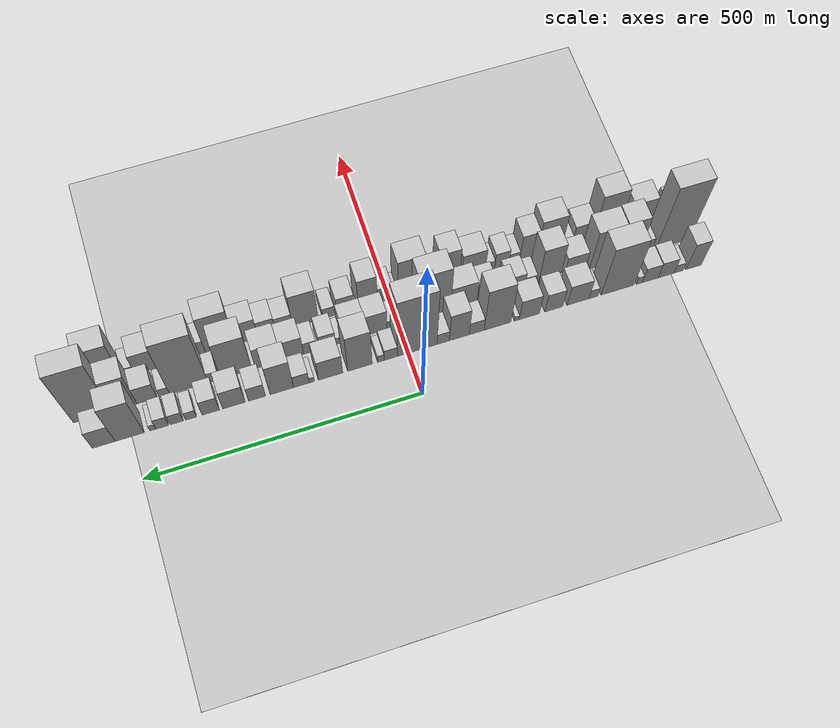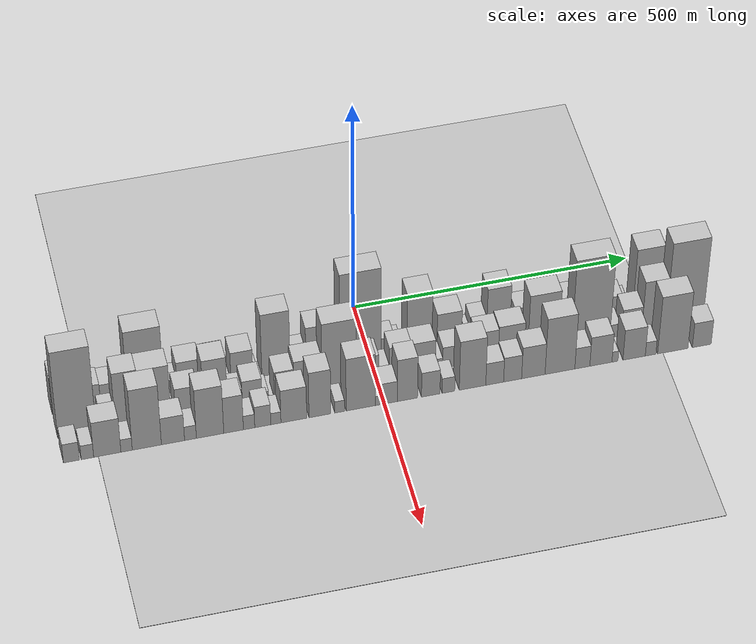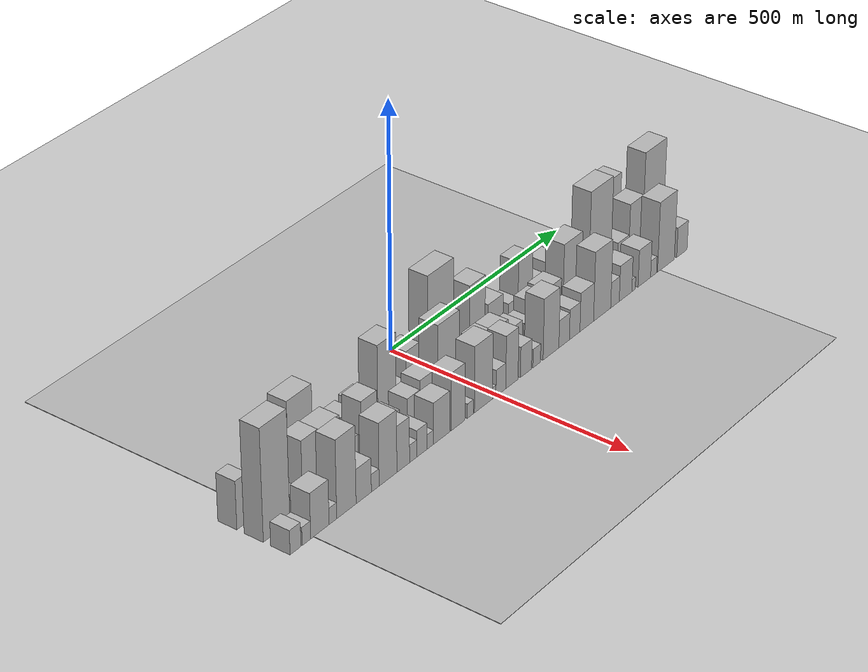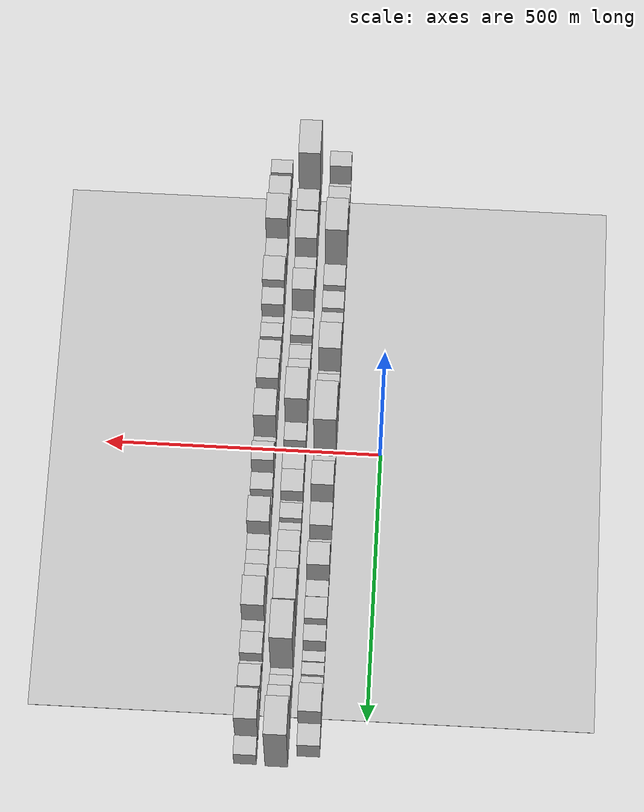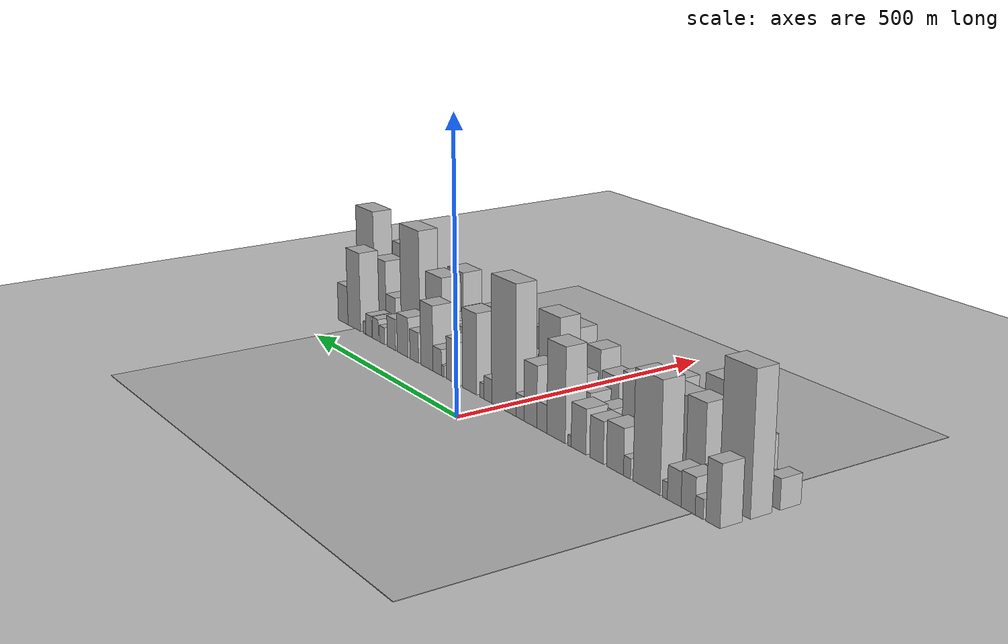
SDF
<?xml version="1.0" encoding="utf-8"?>

<sdf version="1.6">

   <world name="default">

      <gui fullscreen="0">

         <camera name="user_camera">

            <pose>-15 0 4.57585 0 0 0</pose>

            <view_controller>orbit</view_controller>

         </camera>

      </gui>

      <scene>

         <sky>

           <clouds>

             <speed>12</speed>

           </clouds>

         </sky>

         <ambient>0.4 0.4 0.4 1</ambient>

         <background>0.7 0.7 0.7 1</background>

         <shadows>1</shadows>

      </scene>

      <gravity>0 0 -9.8066</gravity>

      <magnetic_field>6e-06 2.3e-05 -4.2e-05</magnetic_field>

      <physics default="0" name="default_physics" type="ode">

         <ode>

            <solver>

               <type>quick</type>

               <iters>10</iters>

               <sor>1.0</sor>

               <use_dynamic_moi_rescaling>0</use_dynamic_moi_rescaling>

            </solver>

            <constraints>

               <cfm>0</cfm>

               <erp>0.2</erp>

               <contact_max_correcting_vel>100</contact_max_correcting_vel>

               <contact_surface_layer>0.001</contact_surface_layer>

            </constraints>

         </ode>

         <max_step_size>0.004</max_step_size>

         <real_time_factor>1</real_time_factor>

         <real_time_update_rate>250</real_time_update_rate>

      </physics>

      <light name="sun" type="directional">

         <cast_shadows>1</cast_shadows>

         <pose>0 0 10 0 0 0</pose>

         <diffuse>0.8 0.8 0.8 1</diffuse>

         <specular>0.2 0.2 0.2 1</specular>

         <attenuation>

            <range>1000</range>

            <constant>0.9</constant>

            <linear>0.01</linear>

            <quadratic>0.001</quadratic>

         </attenuation>

         <direction>-0.5 0.1 -0.9</direction>

      </light>

      <include>

         <name>ground_plane_1</name>

         <uri>model://HANNAS_ground_plane</uri>

         <pose>0 0 0  0 0 0</pose>

      </include>

      <include>

         <name>ground_plane_2</name>

         <uri>model://HANNAS_ground_plane</uri>

         <pose>100 0 0  0 0 0</pose>

      </include>

      <model name="building_1">

         <static>1</static>

         <pose frame="">100.0000 -544.7982 0 0.000000 0.000000 0.000000</pose>

         <link name="link">

            <pose frame="">0 0 48.00 0 0 0</pose>

            <collision name="collision">

               <geometry>

                  <box>

                     <size>40.0000 30.4036 96.0000</size>

                  </box>

               </geometry>

               <max_contacts>10</max_contacts>

               <surface>

                  <contact>

                     <ode/>

                  </contact>

                  <bounce/>

                  <friction>

                     <torsional>

                        <ode/>

                     </torsional>

                     <ode/>

                  </friction>

               </surface>

            </collision>

            <visual name="visual">

               <cast_shadows>0</cast_shadows>

               <geometry>

                  <box>

                     <size>40.0000 30.4036 96.0000</size>

                  </box>

               </geometry>

               <material>

                  <script>

                     <uri>model://HANNAS_wall/materials/scripts</uri>

                     <uri>model://HANNAS_wall/materials/textures</uri>

                     <name>vrc/HANNAS_wall</name>

                  </script>

               </material>

            </visual>

            <self_collide>0</self_collide>

            <enable_wind>0</enable_wind>

            <kinematic>0</kinematic>

         </link>

      </model>

      <model name="building_2">

         <static>1</static>

         <pose frame="">100.0000 -515.6241 0 0.000000 0.000000 0.000000</pose>

         <link name="link">

            <pose frame="">0 0 15.00 0 0 0</pose>

            <collision name="collision">

               <geometry>

                  <box>

                     <size>40.0000 17.9446 30.0000</size>

                  </box>

               </geometry>

               <max_contacts>10</max_contacts>

               <surface>

                  <contact>

                     <ode/>

                  </contact>

                  <bounce/>

                  <friction>

                     <torsional>

                        <ode/>

                     </torsional>

                     <ode/>

                  </friction>

               </surface>

            </collision>

            <visual name="visual">

               <cast_shadows>0</cast_shadows>

               <geometry>

                  <box>

                     <size>40.0000 17.9446 30.0000</size>

                  </box>

               </geometry>

               <material>

                  <script>

                     <uri>model://HANNAS_wall/materials/scripts</uri>

                     <uri>model://HANNAS_wall/materials/textures</uri>

                     <name>vrc/HANNAS_wall</name>

                  </script>

               </material>

            </visual>

            <self_collide>0</self_collide>

            <enable_wind>0</enable_wind>

            <kinematic>0</kinematic>

         </link>

      </model>

      <model name="building_3">

         <static>1</static>

         <pose frame="">100.0000 -491.0013 0 0.000000 0.000000 0.000000</pose>

         <link name="link">

            <pose frame="">0 0 28.50 0 0 0</pose>

            <collision name="collision">

               <geometry>

                  <box>

                     <size>40.0000 31.3010 57.0000</size>

                  </box>

               </geometry>

               <max_contacts>10</max_contacts>

               <surface>

                  <contact>

                     <ode/>

                  </contact>

                  <bounce/>

                  <friction>

                     <torsional>

                        <ode/>

                     </torsional>

                     <ode/>

                  </friction>

               </surface>

            </collision>

            <visual name="visual">

               <cast_shadows>0</cast_shadows>

               <geometry>

                  <box>

                     <size>40.0000 31.3010 57.0000</size>

                  </box>

               </geometry>

               <material>

                  <script>

                     <uri>model://HANNAS_wall/materials/scripts</uri>

                     <uri>model://HANNAS_wall/materials/textures</uri>

                     <name>vrc/HANNAS_wall</name>

                  </script>

               </material>

            </visual>

            <self_collide>0</self_collide>

            <enable_wind>0</enable_wind>

            <kinematic>0</kinematic>

         </link>

      </model>

      <model name="building_4">

         <static>1</static>

         <pose frame="">100.0000 -459.8944 0 0.000000 0.000000 0.000000</pose>

         <link name="link">

            <pose frame="">0 0 27.00 0 0 0</pose>

            <collision name="collision">

               <geometry>

                  <box>

                     <size>40.0000 30.9129 54.0000</size>

                  </box>

               </geometry>

               <max_contacts>10</max_contacts>

               <surface>

                  <contact>

                     <ode/>

                  </contact>

                  <bounce/>

                  <friction>

                     <torsional>

                        <ode/>

                     </torsional>

                     <ode/>

                  </friction>

               </surface>

            </collision>

            <visual name="visual">

               <cast_shadows>0</cast_shadows>

               <geometry>

                  <box>

                     <size>40.0000 30.9129 54.0000</size>

                  </box>

               </geometry>

               <material>

                  <script>

                     <uri>model://HANNAS_wall/materials/scripts</uri>

                     <uri>model://HANNAS_wall/materials/textures</uri>

                     <name>vrc/HANNAS_wall</name>

                  </script>

               </material>

            </visual>

            <self_collide>0</self_collide>

            <enable_wind>0</enable_wind>

            <kinematic>0</kinematic>

         </link>

      </model>

      <model name="building_5">

         <static>1</static>

         <pose frame="">100.0000 -438.7149 0 0.000000 0.000000 0.000000</pose>

         <link name="link">

            <pose frame="">0 0 13.50 0 0 0</pose>

            <collision name="collision">

               <geometry>

                  <box>

                     <size>40.0000 11.4460 27.0000</size>

                  </box>

               </geometry>

               <max_contacts>10</max_contacts>

               <surface>

                  <contact>

                     <ode/>

                  </contact>

                  <bounce/>

                  <friction>

                     <torsional>

                        <ode/>

                     </torsional>

                     <ode/>

                  </friction>

               </surface>

            </collision>

            <visual name="visual">

               <cast_shadows>0</cast_shadows>

               <geometry>

                  <box>

                     <size>40.0000 11.4460 27.0000</size>

                  </box>

               </geometry>

               <material>

                  <script>

                     <uri>model://HANNAS_wall/materials/scripts</uri>

                     <uri>model://HANNAS_wall/materials/textures</uri>

                     <name>vrc/HANNAS_wall</name>

                  </script>

               </material>

            </visual>

            <self_collide>0</self_collide>

            <enable_wind>0</enable_wind>

            <kinematic>0</kinematic>

         </link>

      </model>

      <model name="building_6">

         <static>1</static>

         <pose frame="">100.0000 -396.0838 0 0.000000 0.000000 0.000000</pose>

         <link name="link">

            <pose frame="">0 0 88.50 0 0 0</pose>

            <collision name="collision">

               <geometry>

                  <box>

                     <size>40.0000 63.8163 177.0000</size>

                  </box>

               </geometry>

               <max_contacts>10</max_contacts>

               <surface>

                  <contact>

                     <ode/>

                  </contact>

                  <bounce/>

                  <friction>

                     <torsional>

                        <ode/>

                     </torsional>

                     <ode/>

                  </friction>

               </surface>

            </collision>

            <visual name="visual">

               <cast_shadows>0</cast_shadows>

               <geometry>

                  <box>

                     <size>40.0000 63.8163 177.0000</size>

                  </box>

               </geometry>

               <material>

                  <script>

                     <uri>model://HANNAS_wall/materials/scripts</uri>

                     <uri>model://HANNAS_wall/materials/textures</uri>

                     <name>vrc/HANNAS_wall</name>

                  </script>

               </material>

            </visual>

            <self_collide>0</self_collide>

            <enable_wind>0</enable_wind>

            <kinematic>0</kinematic>

         </link>

      </model>

      <model name="building_7">

         <static>1</static>

         <pose frame="">100.0000 -349.6502 0 0.000000 0.000000 0.000000</pose>

         <link name="link">

            <pose frame="">0 0 16.50 0 0 0</pose>

            <collision name="collision">

               <geometry>

                  <box>

                     <size>40.0000 17.0509 33.0000</size>

                  </box>

               </geometry>

               <max_contacts>10</max_contacts>

               <surface>

                  <contact>

                     <ode/>

                  </contact>

                  <bounce/>

                  <friction>

                     <torsional>

                        <ode/>

                     </torsional>

                     <ode/>

                  </friction>

               </surface>

            </collision>

            <visual name="visual">

               <cast_shadows>0</cast_shadows>

               <geometry>

                  <box>

                     <size>40.0000 17.0509 33.0000</size>

                  </box>

               </geometry>

               <material>

                  <script>

                     <uri>model://HANNAS_wall/materials/scripts</uri>

                     <uri>model://HANNAS_wall/materials/textures</uri>

                     <name>vrc/HANNAS_wall</name>

                  </script>

               </material>

            </visual>

            <self_collide>0</self_collide>

            <enable_wind>0</enable_wind>

            <kinematic>0</kinematic>

         </link>

      </model>

      <model name="building_8">

         <static>1</static>

         <pose frame="">100.0000 -319.9819 0 0.000000 0.000000 0.000000</pose>

         <link name="link">

            <pose frame="">0 0 37.50 0 0 0</pose>

            <collision name="collision">

               <geometry>

                  <box>

                     <size>40.0000 42.2859 75.0000</size>

                  </box>

               </geometry>

               <max_contacts>10</max_contacts>

               <surface>

                  <contact>

                     <ode/>

                  </contact>

                  <bounce/>

                  <friction>

                     <torsional>

                        <ode/>

                     </torsional>

                     <ode/>

                  </friction>

               </surface>

            </collision>

            <visual name="visual">

               <cast_shadows>0</cast_shadows>

               <geometry>

                  <box>

                     <size>40.0000 42.2859 75.0000</size>

                  </box>

               </geometry>

               <material>

                  <script>

                     <uri>model://HANNAS_wall/materials/scripts</uri>

                     <uri>model://HANNAS_wall/materials/textures</uri>

                     <name>vrc/HANNAS_wall</name>

                  </script>

               </material>

            </visual>

            <self_collide>0</self_collide>

            <enable_wind>0</enable_wind>

            <kinematic>0</kinematic>

         </link>

      </model>

      <model name="building_9">

         <static>1</static>

         <pose frame="">100.0000 -273.5567 0 0.000000 0.000000 0.000000</pose>

         <link name="link">

            <pose frame="">0 0 34.50 0 0 0</pose>

            <collision name="collision">

               <geometry>

                  <box>

                     <size>40.0000 34.5645 69.0000</size>

                  </box>

               </geometry>

               <max_contacts>10</max_contacts>

               <surface>

                  <contact>

                     <ode/>

                  </contact>

                  <bounce/>

                  <friction>

                     <torsional>

                        <ode/>

                     </torsional>

                     <ode/>

                  </friction>

               </surface>

            </collision>

            <visual name="visual">

               <cast_shadows>0</cast_shadows>

               <geometry>

                  <box>

                     <size>40.0000 34.5645 69.0000</size>

                  </box>

               </geometry>

               <material>

                  <script>

                     <uri>model://HANNAS_wall/materials/scripts</uri>

                     <uri>model://HANNAS_wall/materials/textures</uri>

                     <name>vrc/HANNAS_wall</name>

                  </script>

               </material>

            </visual>

            <self_collide>0</self_collide>

            <enable_wind>0</enable_wind>

            <kinematic>0</kinematic>

         </link>

      </model>

      <model name="building_10">

         <static>1</static>

         <pose frame="">100.0000 -226.8412 0 0.000000 0.000000 0.000000</pose>

         <link name="link">

            <pose frame="">0 0 37.50 0 0 0</pose>

            <collision name="collision">

               <geometry>

                  <box>

                     <size>40.0000 38.8664 75.0000</size>

                  </box>

               </geometry>

               <max_contacts>10</max_contacts>

               <surface>

                  <contact>

                     <ode/>

                  </contact>

                  <bounce/>

                  <friction>

                     <torsional>

                        <ode/>

                     </torsional>

                     <ode/>

                  </friction>

               </surface>

            </collision>

            <visual name="visual">

               <cast_shadows>0</cast_shadows>

               <geometry>

                  <box>

                     <size>40.0000 38.8664 75.0000</size>

                  </box>

               </geometry>

               <material>

                  <script>

                     <uri>model://HANNAS_wall/materials/scripts</uri>

                     <uri>model://HANNAS_wall/materials/textures</uri>

                     <name>vrc/HANNAS_wall</name>

                  </script>

               </material>

            </visual>

            <self_collide>0</self_collide>

            <enable_wind>0</enable_wind>

            <kinematic>0</kinematic>

         </link>

      </model>

      <model name="building_11">

         <static>1</static>

         <pose frame="">100.0000 -202.9946 0 0.000000 0.000000 0.000000</pose>

         <link name="link">

            <pose frame="">0 0 9.00 0 0 0</pose>

            <collision name="collision">

               <geometry>

                  <box>

                     <size>40.0000 8.8269 18.0000</size>

                  </box>

               </geometry>

               <max_contacts>10</max_contacts>

               <surface>

                  <contact>

                     <ode/>

                  </contact>

                  <bounce/>

                  <friction>

                     <torsional>

                        <ode/>

                     </torsional>

                     <ode/>

                  </friction>

               </surface>

            </collision>

            <visual name="visual">

               <cast_shadows>0</cast_shadows>

               <geometry>

                  <box>

                     <size>40.0000 8.8269 18.0000</size>

                  </box>

               </geometry>

               <material>

                  <script>

                     <uri>model://HANNAS_wall/materials/scripts</uri>

                     <uri>model://HANNAS_wall/materials/textures</uri>

                     <name>vrc/HANNAS_wall</name>

                  </script>

               </material>

            </visual>

            <self_collide>0</self_collide>

            <enable_wind>0</enable_wind>

            <kinematic>0</kinematic>

         </link>

      </model>

      <model name="building_12">

         <static>1</static>

         <pose frame="">100.0000 -166.4105 0 0.000000 0.000000 0.000000</pose>

         <link name="link">

            <pose frame="">0 0 79.50 0 0 0</pose>

            <collision name="collision">

               <geometry>

                  <box>

                     <size>40.0000 50.3411 159.0000</size>

                  </box>

               </geometry>

               <max_contacts>10</max_contacts>

               <surface>

                  <contact>

                     <ode/>

                  </contact>

                  <bounce/>

                  <friction>

                     <torsional>

                        <ode/>

                     </torsional>

                     <ode/>

                  </friction>

               </surface>

            </collision>

            <visual name="visual">

               <cast_shadows>0</cast_shadows>

               <geometry>

                  <box>

                     <size>40.0000 50.3411 159.0000</size>

                  </box>

               </geometry>

               <material>

                  <script>

                     <uri>model://HANNAS_wall/materials/scripts</uri>

                     <uri>model://HANNAS_wall/materials/textures</uri>

                     <name>vrc/HANNAS_wall</name>

                  </script>

               </material>

            </visual>

            <self_collide>0</self_collide>

            <enable_wind>0</enable_wind>

            <kinematic>0</kinematic>

         </link>

      </model>

      <model name="building_13">

         <static>1</static>

         <pose frame="">100.0000 -127.2518 0 0.000000 0.000000 0.000000</pose>

         <link name="link">

            <pose frame="">0 0 24.00 0 0 0</pose>

            <collision name="collision">

               <geometry>

                  <box>

                     <size>40.0000 27.9762 48.0000</size>

                  </box>

               </geometry>

               <max_contacts>10</max_contacts>

               <surface>

                  <contact>

                     <ode/>

                  </contact>

                  <bounce/>

                  <friction>

                     <torsional>

                        <ode/>

                     </torsional>

                     <ode/>

                  </friction>

               </surface>

            </collision>

            <visual name="visual">

               <cast_shadows>0</cast_shadows>

               <geometry>

                  <box>

                     <size>40.0000 27.9762 48.0000</size>

                  </box>

               </geometry>

               <material>

                  <script>

                     <uri>model://HANNAS_wall/materials/scripts</uri>

                     <uri>model://HANNAS_wall/materials/textures</uri>

                     <name>vrc/HANNAS_wall</name>

                  </script>

               </material>

            </visual>

            <self_collide>0</self_collide>

            <enable_wind>0</enable_wind>

            <kinematic>0</kinematic>

         </link>

      </model>

      <model name="building_14">

         <static>1</static>

         <pose frame="">100.0000 -94.5568 0 0.000000 0.000000 0.000000</pose>

         <link name="link">

            <pose frame="">0 0 52.50 0 0 0</pose>

            <collision name="collision">

               <geometry>

                  <box>

                     <size>40.0000 37.4138 105.0000</size>

                  </box>

               </geometry>

               <max_contacts>10</max_contacts>

               <surface>

                  <contact>

                     <ode/>

                  </contact>

                  <bounce/>

                  <friction>

                     <torsional>

                        <ode/>

                     </torsional>

                     <ode/>

                  </friction>

               </surface>

            </collision>

            <visual name="visual">

               <cast_shadows>0</cast_shadows>

               <geometry>

                  <box>

                     <size>40.0000 37.4138 105.0000</size>

                  </box>

               </geometry>

               <material>

                  <script>

                     <uri>model://HANNAS_wall/materials/scripts</uri>

                     <uri>model://HANNAS_wall/materials/textures</uri>

                     <name>vrc/HANNAS_wall</name>

                  </script>

               </material>

            </visual>

            <self_collide>0</self_collide>

            <enable_wind>0</enable_wind>

            <kinematic>0</kinematic>

         </link>

      </model>

      <model name="building_15">

         <static>1</static>

         <pose frame="">100.0000 -64.4042 0 0.000000 0.000000 0.000000</pose>

         <link name="link">

            <pose frame="">0 0 21.00 0 0 0</pose>

            <collision name="collision">

               <geometry>

                  <box>

                     <size>40.0000 22.8915 42.0000</size>

                  </box>

               </geometry>

               <max_contacts>10</max_contacts>

               <surface>

                  <contact>

                     <ode/>

                  </contact>

                  <bounce/>

                  <friction>

                     <torsional>

                        <ode/>

                     </torsional>

                     <ode/>

                  </friction>

               </surface>

            </collision>

            <visual name="visual">

               <cast_shadows>0</cast_shadows>

               <geometry>

                  <box>

                     <size>40.0000 22.8915 42.0000</size>

                  </box>

               </geometry>

               <material>

                  <script>

                     <uri>model://HANNAS_wall/materials/scripts</uri>

                     <uri>model://HANNAS_wall/materials/textures</uri>

                     <name>vrc/HANNAS_wall</name>

                  </script>

               </material>

            </visual>

            <self_collide>0</self_collide>

            <enable_wind>0</enable_wind>

            <kinematic>0</kinematic>

         </link>

      </model>

      <model name="building_16">

         <static>1</static>

         <pose frame="">100.0000 -16.2059 0 0.000000 0.000000 0.000000</pose>

         <link name="link">

            <pose frame="">0 0 112.50 0 0 0</pose>

            <collision name="collision">

               <geometry>

                  <box>

                     <size>40.0000 73.5050 225.0000</size>

                  </box>

               </geometry>

               <max_contacts>10</max_contacts>

               <surface>

                  <contact>

                     <ode/>

                  </contact>

                  <bounce/>

                  <friction>

                     <torsional>

                        <ode/>

                     </torsional>

                     <ode/>

                  </friction>

               </surface>

            </collision>

            <visual name="visual">

               <cast_shadows>0</cast_shadows>

               <geometry>

                  <box>

                     <size>40.0000 73.5050 225.0000</size>

                  </box>

               </geometry>

               <material>

                  <script>

                     <uri>model://HANNAS_wall/materials/scripts</uri>

                     <uri>model://HANNAS_wall/materials/textures</uri>

                     <name>vrc/HANNAS_wall</name>

                  </script>

               </material>

            </visual>

            <self_collide>0</self_collide>

            <enable_wind>0</enable_wind>

            <kinematic>0</kinematic>

         </link>

      </model>

      <model name="building_17">

         <static>1</static>

         <pose frame="">100.0000 32.7443 0 0.000000 0.000000 0.000000</pose>

         <link name="link">

            <pose frame="">0 0 21.00 0 0 0</pose>

            <collision name="collision">

               <geometry>

                  <box>

                     <size>40.0000 24.3954 42.0000</size>

                  </box>

               </geometry>

               <max_contacts>10</max_contacts>

               <surface>

                  <contact>

                     <ode/>

                  </contact>

                  <bounce/>

                  <friction>

                     <torsional>

                        <ode/>

                     </torsional>

                     <ode/>

                  </friction>

               </surface>

            </collision>

            <visual name="visual">

               <cast_shadows>0</cast_shadows>

               <geometry>

                  <box>

                     <size>40.0000 24.3954 42.0000</size>

                  </box>

               </geometry>

               <material>

                  <script>

                     <uri>model://HANNAS_wall/materials/scripts</uri>

                     <uri>model://HANNAS_wall/materials/textures</uri>

                     <name>vrc/HANNAS_wall</name>

                  </script>

               </material>

            </visual>

            <self_collide>0</self_collide>

            <enable_wind>0</enable_wind>

            <kinematic>0</kinematic>

         </link>

      </model>

      <model name="building_18">

         <static>1</static>

         <pose frame="">100.0000 51.1259 0 0.000000 0.000000 0.000000</pose>

         <link name="link">

            <pose frame="">0 0 13.50 0 0 0</pose>

            <collision name="collision">

               <geometry>

                  <box>

                     <size>40.0000 12.3677 27.0000</size>

                  </box>

               </geometry>

               <max_contacts>10</max_contacts>

               <surface>

                  <contact>

                     <ode/>

                  </contact>

                  <bounce/>

                  <friction>

                     <torsional>

                        <ode/>

                     </torsional>

                     <ode/>

                  </friction>

               </surface>

            </collision>

            <visual name="visual">

               <cast_shadows>0</cast_shadows>

               <geometry>

                  <box>

                     <size>40.0000 12.3677 27.0000</size>

                  </box>

               </geometry>

               <material>

                  <script>

                     <uri>model://HANNAS_wall/materials/scripts</uri>

                     <uri>model://HANNAS_wall/materials/textures</uri>

                     <name>vrc/HANNAS_wall</name>

                  </script>

               </material>

            </visual>

            <self_collide>0</self_collide>

            <enable_wind>0</enable_wind>

            <kinematic>0</kinematic>

         </link>

      </model>

      <model name="building_19">

         <static>1</static>

         <pose frame="">100.0000 89.8084 0 0.000000 0.000000 0.000000</pose>

         <link name="link">

            <pose frame="">0 0 72.00 0 0 0</pose>

            <collision name="collision">

               <geometry>

                  <box>

                     <size>40.0000 44.9975 144.0000</size>

                  </box>

               </geometry>

               <max_contacts>10</max_contacts>

               <surface>

                  <contact>

                     <ode/>

                  </contact>

                  <bounce/>

                  <friction>

                     <torsional>

                        <ode/>

                     </torsional>

                     <ode/>

                  </friction>

               </surface>

            </collision>

            <visual name="visual">

               <cast_shadows>0</cast_shadows>

               <geometry>

                  <box>

                     <size>40.0000 44.9975 144.0000</size>

                  </box>

               </geometry>

               <material>

                  <script>

                     <uri>model://HANNAS_wall/materials/scripts</uri>

                     <uri>model://HANNAS_wall/materials/textures</uri>

                     <name>vrc/HANNAS_wall</name>

                  </script>

               </material>

            </visual>

            <self_collide>0</self_collide>

            <enable_wind>0</enable_wind>

            <kinematic>0</kinematic>

         </link>

      </model>

      <model name="building_20">

         <static>1</static>

         <pose frame="">100.0000 143.5928 0 0.000000 0.000000 0.000000</pose>

         <link name="link">

            <pose frame="">0 0 39.00 0 0 0</pose>

            <collision name="collision">

               <geometry>

                  <box>

                     <size>40.0000 44.5713 78.0000</size>

                  </box>

               </geometry>

               <max_contacts>10</max_contacts>

               <surface>

                  <contact>

                     <ode/>

                  </contact>

                  <bounce/>

                  <friction>

                     <torsional>

                        <ode/>

                     </torsional>

                     <ode/>

                  </friction>

               </surface>

            </collision>

            <visual name="visual">

               <cast_shadows>0</cast_shadows>

               <geometry>

                  <box>

                     <size>40.0000 44.5713 78.0000</size>

                  </box>

               </geometry>

               <material>

                  <script>

                     <uri>model://HANNAS_wall/materials/scripts</uri>

                     <uri>model://HANNAS_wall/materials/textures</uri>

                     <name>vrc/HANNAS_wall</name>

                  </script>

               </material>

            </visual>

            <self_collide>0</self_collide>

            <enable_wind>0</enable_wind>

            <kinematic>0</kinematic>

         </link>

      </model>

      <model name="building_21">

         <static>1</static>

         <pose frame="">100.0000 177.5713 0 0.000000 0.000000 0.000000</pose>

         <link name="link">

            <pose frame="">0 0 10.50 0 0 0</pose>

            <collision name="collision">

               <geometry>

                  <box>

                     <size>40.0000 9.3858 21.0000</size>

                  </box>

               </geometry>

               <max_contacts>10</max_contacts>

               <surface>

                  <contact>

                     <ode/>

                  </contact>

                  <bounce/>

                  <friction>

                     <torsional>

                        <ode/>

                     </torsional>

                     <ode/>

                  </friction>

               </surface>

            </collision>

            <visual name="visual">

               <cast_shadows>0</cast_shadows>

               <geometry>

                  <box>

                     <size>40.0000 9.3858 21.0000</size>

                  </box>

               </geometry>

               <material>

                  <script>

                     <uri>model://HANNAS_wall/materials/scripts</uri>

                     <uri>model://HANNAS_wall/materials/textures</uri>

                     <name>vrc/HANNAS_wall</name>

                  </script>

               </material>

            </visual>

            <self_collide>0</self_collide>

            <enable_wind>0</enable_wind>

            <kinematic>0</kinematic>

         </link>

      </model>

      <model name="building_22">

         <static>1</static>

         <pose frame="">100.0000 196.5249 0 0.000000 0.000000 0.000000</pose>

         <link name="link">

            <pose frame="">0 0 24.00 0 0 0</pose>

            <collision name="collision">

               <geometry>

                  <box>

                     <size>40.0000 28.5214 48.0000</size>

                  </box>

               </geometry>

               <max_contacts>10</max_contacts>

               <surface>

                  <contact>

                     <ode/>

                  </contact>

                  <bounce/>

                  <friction>

                     <torsional>

                        <ode/>

                     </torsional>

                     <ode/>

                  </friction>

               </surface>

            </collision>

            <visual name="visual">

               <cast_shadows>0</cast_shadows>

               <geometry>

                  <box>

                     <size>40.0000 28.5214 48.0000</size>

                  </box>

               </geometry>

               <material>

                  <script>

                     <uri>model://HANNAS_wall/materials/scripts</uri>

                     <uri>model://HANNAS_wall/materials/textures</uri>

                     <name>vrc/HANNAS_wall</name>

                  </script>

               </material>

            </visual>

            <self_collide>0</self_collide>

            <enable_wind>0</enable_wind>

            <kinematic>0</kinematic>

         </link>

      </model>

      <model name="building_23">

         <static>1</static>

         <pose frame="">100.0000 232.0757 0 0.000000 0.000000 0.000000</pose>

         <link name="link">

            <pose frame="">0 0 60.00 0 0 0</pose>

            <collision name="collision">

               <geometry>

                  <box>

                     <size>40.0000 42.5802 120.0000</size>

                  </box>

               </geometry>

               <max_contacts>10</max_contacts>

               <surface>

                  <contact>

                     <ode/>

                  </contact>

                  <bounce/>

                  <friction>

                     <torsional>

                        <ode/>

                     </torsional>

                     <ode/>

                  </friction>

               </surface>

            </collision>

            <visual name="visual">

               <cast_shadows>0</cast_shadows>

               <geometry>

                  <box>

                     <size>40.0000 42.5802 120.0000</size>

                  </box>

               </geometry>

               <material>

                  <script>

                     <uri>model://HANNAS_wall/materials/scripts</uri>

                     <uri>model://HANNAS_wall/materials/textures</uri>

                     <name>vrc/HANNAS_wall</name>

                  </script>

               </material>

            </visual>

            <self_collide>0</self_collide>

            <enable_wind>0</enable_wind>

            <kinematic>0</kinematic>

         </link>

      </model>

      <model name="building_24">

         <static>1</static>

         <pose frame="">100.0000 276.7771 0 0.000000 0.000000 0.000000</pose>

         <link name="link">

            <pose frame="">0 0 28.50 0 0 0</pose>

            <collision name="collision">

               <geometry>

                  <box>

                     <size>40.0000 30.8225 57.0000</size>

                  </box>

               </geometry>

               <max_contacts>10</max_contacts>

               <surface>

                  <contact>

                     <ode/>

                  </contact>

                  <bounce/>

                  <friction>

                     <torsional>

                        <ode/>

                     </torsional>

                     <ode/>

                  </friction>

               </surface>

            </collision>

            <visual name="visual">

               <cast_shadows>0</cast_shadows>

               <geometry>

                  <box>

                     <size>40.0000 30.8225 57.0000</size>

                  </box>

               </geometry>

               <material>

                  <script>

                     <uri>model://HANNAS_wall/materials/scripts</uri>

                     <uri>model://HANNAS_wall/materials/textures</uri>

                     <name>vrc/HANNAS_wall</name>

                  </script>

               </material>

            </visual>

            <self_collide>0</self_collide>

            <enable_wind>0</enable_wind>

            <kinematic>0</kinematic>

         </link>

      </model>

      <model name="building_25">

         <static>1</static>

         <pose frame="">100.0000 318.3123 0 0.000000 0.000000 0.000000</pose>

         <link name="link">

            <pose frame="">0 0 37.50 0 0 0</pose>

            <collision name="collision">

               <geometry>

                  <box>

                     <size>40.0000 40.2480 75.0000</size>

                  </box>

               </geometry>

               <max_contacts>10</max_contacts>

               <surface>

                  <contact>

                     <ode/>

                  </contact>

                  <bounce/>

                  <friction>

                     <torsional>

                        <ode/>

                     </torsional>

                     <ode/>

                  </friction>

               </surface>

            </collision>

            <visual name="visual">

               <cast_shadows>0</cast_shadows>

               <geometry>

                  <box>

                     <size>40.0000 40.2480 75.0000</size>

                  </box>

               </geometry>

               <material>

                  <script>

                     <uri>model://HANNAS_wall/materials/scripts</uri>

                     <uri>model://HANNAS_wall/materials/textures</uri>

                     <name>vrc/HANNAS_wall</name>

                  </script>

               </material>

            </visual>

            <self_collide>0</self_collide>

            <enable_wind>0</enable_wind>

            <kinematic>0</kinematic>

         </link>

      </model>

      <model name="building_26">

         <static>1</static>

         <pose frame="">100.0000 359.7797 0 0.000000 0.000000 0.000000</pose>

         <link name="link">

            <pose frame="">0 0 30.00 0 0 0</pose>

            <collision name="collision">

               <geometry>

                  <box>

                     <size>40.0000 30.6868 60.0000</size>

                  </box>

               </geometry>

               <max_contacts>10</max_contacts>

               <surface>

                  <contact>

                     <ode/>

                  </contact>

                  <bounce/>

                  <friction>

                     <torsional>

                        <ode/>

                     </torsional>

                     <ode/>

                  </friction>

               </surface>

            </collision>

            <visual name="visual">

               <cast_shadows>0</cast_shadows>

               <geometry>

                  <box>

                     <size>40.0000 30.6868 60.0000</size>

                  </box>

               </geometry>

               <material>

                  <script>

                     <uri>model://HANNAS_wall/materials/scripts</uri>

                     <uri>model://HANNAS_wall/materials/textures</uri>

                     <name>vrc/HANNAS_wall</name>

                  </script>

               </material>

            </visual>

            <self_collide>0</self_collide>

            <enable_wind>0</enable_wind>

            <kinematic>0</kinematic>

         </link>

      </model>

      <model name="building_27">

         <static>1</static>

         <pose frame="">100.0000 394.9521 0 0.000000 0.000000 0.000000</pose>

         <link name="link">

            <pose frame="">0 0 16.50 0 0 0</pose>

            <collision name="collision">

               <geometry>

                  <box>

                     <size>40.0000 19.6581 33.0000</size>

                  </box>

               </geometry>

               <max_contacts>10</max_contacts>

               <surface>

                  <contact>

                     <ode/>

                  </contact>

                  <bounce/>

                  <friction>

                     <torsional>

                        <ode/>

                     </torsional>

                     <ode/>

                  </friction>

               </surface>

            </collision>

            <visual name="visual">

               <cast_shadows>0</cast_shadows>

               <geometry>

                  <box>

                     <size>40.0000 19.6581 33.0000</size>

                  </box>

               </geometry>

               <material>

                  <script>

                     <uri>model://HANNAS_wall/materials/scripts</uri>

                     <uri>model://HANNAS_wall/materials/textures</uri>

                     <name>vrc/HANNAS_wall</name>

                  </script>

               </material>

            </visual>

            <self_collide>0</self_collide>

            <enable_wind>0</enable_wind>

            <kinematic>0</kinematic>

         </link>

      </model>

      <model name="building_28">

         <static>1</static>

         <pose frame="">100.0000 420.2818 0 0.000000 0.000000 0.000000</pose>

         <link name="link">

            <pose frame="">0 0 21.00 0 0 0</pose>

            <collision name="collision">

               <geometry>

                  <box>

                     <size>40.0000 23.0011 42.0000</size>

                  </box>

               </geometry>

               <max_contacts>10</max_contacts>

               <surface>

                  <contact>

                     <ode/>

                  </contact>

                  <bounce/>

                  <friction>

                     <torsional>

                        <ode/>

                     </torsional>

                     <ode/>

                  </friction>

               </surface>

            </collision>

            <visual name="visual">

               <cast_shadows>0</cast_shadows>

               <geometry>

                  <box>

                     <size>40.0000 23.0011 42.0000</size>

                  </box>

               </geometry>

               <material>

                  <script>

                     <uri>model://HANNAS_wall/materials/scripts</uri>

                     <uri>model://HANNAS_wall/materials/textures</uri>

                     <name>vrc/HANNAS_wall</name>

                  </script>

               </material>

            </visual>

            <self_collide>0</self_collide>

            <enable_wind>0</enable_wind>

            <kinematic>0</kinematic>

         </link>

      </model>

      <model name="building_29">

         <static>1</static>

         <pose frame="">100.0000 446.0894 0 0.000000 0.000000 0.000000</pose>

         <link name="link">

            <pose frame="">0 0 21.00 0 0 0</pose>

            <collision name="collision">

               <geometry>

                  <box>

                     <size>40.0000 22.6141 42.0000</size>

                  </box>

               </geometry>

               <max_contacts>10</max_contacts>

               <surface>

                  <contact>

                     <ode/>

                  </contact>

                  <bounce/>

                  <friction>

                     <torsional>

                        <ode/>

                     </torsional>

                     <ode/>

                  </friction>

               </surface>

            </collision>

            <visual name="visual">

               <cast_shadows>0</cast_shadows>

               <geometry>

                  <box>

                     <size>40.0000 22.6141 42.0000</size>

                  </box>

               </geometry>

               <material>

                  <script>

                     <uri>model://HANNAS_wall/materials/scripts</uri>

                     <uri>model://HANNAS_wall/materials/textures</uri>

                     <name>vrc/HANNAS_wall</name>

                  </script>

               </material>

            </visual>

            <self_collide>0</self_collide>

            <enable_wind>0</enable_wind>

            <kinematic>0</kinematic>

         </link>

      </model>

      <model name="building_30">

         <static>1</static>

         <pose frame="">100.0000 462.6450 0 0.000000 0.000000 0.000000</pose>

         <link name="link">

            <pose frame="">0 0 12.00 0 0 0</pose>

            <collision name="collision">

               <geometry>

                  <box>

                     <size>40.0000 10.4972 24.0000</size>

                  </box>

               </geometry>

               <max_contacts>10</max_contacts>

               <surface>

                  <contact>

                     <ode/>

                  </contact>

                  <bounce/>

                  <friction>

                     <torsional>

                        <ode/>

                     </torsional>

                     <ode/>

                  </friction>

               </surface>

            </collision>

            <visual name="visual">

               <cast_shadows>0</cast_shadows>

               <geometry>

                  <box>

                     <size>40.0000 10.4972 24.0000</size>

                  </box>

               </geometry>

               <material>

                  <script>

                     <uri>model://HANNAS_wall/materials/scripts</uri>

                     <uri>model://HANNAS_wall/materials/textures</uri>

                     <name>vrc/HANNAS_wall</name>

                  </script>

               </material>

            </visual>

            <self_collide>0</self_collide>

            <enable_wind>0</enable_wind>

            <kinematic>0</kinematic>

         </link>

      </model>

      <model name="building_31">

         <static>1</static>

         <pose frame="">100.0000 503.3871 0 0.000000 0.000000 0.000000</pose>

         <link name="link">

            <pose frame="">0 0 76.50 0 0 0</pose>

            <collision name="collision">

               <geometry>

                  <box>

                     <size>40.0000 50.9870 153.0000</size>

                  </box>

               </geometry>

               <max_contacts>10</max_contacts>

               <surface>

                  <contact>

                     <ode/>

                  </contact>

                  <bounce/>

                  <friction>

                     <torsional>

                        <ode/>

                     </torsional>

                     <ode/>

                  </friction>

               </surface>

            </collision>

            <visual name="visual">

               <cast_shadows>0</cast_shadows>

               <geometry>

                  <box>

                     <size>40.0000 50.9870 153.0000</size>

                  </box>

               </geometry>

               <material>

                  <script>

                     <uri>model://HANNAS_wall/materials/scripts</uri>

                     <uri>model://HANNAS_wall/materials/textures</uri>

                     <name>vrc/HANNAS_wall</name>

                  </script>

               </material>

            </visual>

            <self_collide>0</self_collide>

            <enable_wind>0</enable_wind>

            <kinematic>0</kinematic>

         </link>

      </model>

      <model name="building_32">

         <static>1</static>

         <pose frame="">100.0000 548.8465 0 0.000000 0.000000 0.000000</pose>

         <link name="link">

            <pose frame="">0 0 37.50 0 0 0</pose>

            <collision name="collision">

               <geometry>

                  <box>

                     <size>40.0000 39.9317 75.0000</size>

                  </box>

               </geometry>

               <max_contacts>10</max_contacts>

               <surface>

                  <contact>

                     <ode/>

                  </contact>

                  <bounce/>

                  <friction>

                     <torsional>

                        <ode/>

                     </torsional>

                     <ode/>

                  </friction>

               </surface>

            </collision>

            <visual name="visual">

               <cast_shadows>0</cast_shadows>

               <geometry>

                  <box>

                     <size>40.0000 39.9317 75.0000</size>

                  </box>

               </geometry>

               <material>

                  <script>

                     <uri>model://HANNAS_wall/materials/scripts</uri>

                     <uri>model://HANNAS_wall/materials/textures</uri>

                     <name>vrc/HANNAS_wall</name>

                  </script>

               </material>

            </visual>

            <self_collide>0</self_collide>

            <enable_wind>0</enable_wind>

            <kinematic>0</kinematic>

         </link>

      </model>

      <model name="building_33">

         <static>1</static>

         <pose frame="">155.0000 -526.5621 0 0.000000 0.000000 0.000000</pose>

         <link name="link">

            <pose frame="">0 0 111.00 0 0 0</pose>

            <collision name="collision">

               <geometry>

                  <box>

                     <size>40.0000 66.8757 222.0000</size>

                  </box>

               </geometry>

               <max_contacts>10</max_contacts>

               <surface>

                  <contact>

                     <ode/>

                  </contact>

                  <bounce/>

                  <friction>

                     <torsional>

                        <ode/>

                     </torsional>

                     <ode/>

                  </friction>

               </surface>

            </collision>

            <visual name="visual">

               <cast_shadows>0</cast_shadows>

               <geometry>

                  <box>

                     <size>40.0000 66.8757 222.0000</size>

                  </box>

               </geometry>

               <material>

                  <script>

                     <uri>model://HANNAS_wall/materials/scripts</uri>

                     <uri>model://HANNAS_wall/materials/textures</uri>

                     <name>vrc/HANNAS_wall</name>

                  </script>

               </material>

            </visual>

            <self_collide>0</self_collide>

            <enable_wind>0</enable_wind>

            <kinematic>0</kinematic>

         </link>

      </model>

      <model name="building_34">

         <static>1</static>

         <pose frame="">155.0000 -472.5020 0 0.000000 0.000000 0.000000</pose>

         <link name="link">

            <pose frame="">0 0 24.00 0 0 0</pose>

            <collision name="collision">

               <geometry>

                  <box>

                     <size>40.0000 25.2444 48.0000</size>

                  </box>

               </geometry>

               <max_contacts>10</max_contacts>

               <surface>

                  <contact>

                     <ode/>

                  </contact>

                  <bounce/>

                  <friction>

                     <torsional>

                        <ode/>

                     </torsional>

                     <ode/>

                  </friction>

               </surface>

            </collision>

            <visual name="visual">

               <cast_shadows>0</cast_shadows>

               <geometry>

                  <box>

                     <size>40.0000 25.2444 48.0000</size>

                  </box>

               </geometry>

               <material>

                  <script>

                     <uri>model://HANNAS_wall/materials/scripts</uri>

                     <uri>model://HANNAS_wall/materials/textures</uri>

                     <name>vrc/HANNAS_wall</name>

                  </script>

               </material>

            </visual>

            <self_collide>0</self_collide>

            <enable_wind>0</enable_wind>

            <kinematic>0</kinematic>

         </link>

      </model>

      <model name="building_35">

         <static>1</static>

         <pose frame="">155.0000 -438.7280 0 0.000000 0.000000 0.000000</pose>

         <link name="link">

            <pose frame="">0 0 70.50 0 0 0</pose>

            <collision name="collision">

               <geometry>

                  <box>

                     <size>40.0000 42.3037 141.0000</size>

                  </box>

               </geometry>

               <max_contacts>10</max_contacts>

               <surface>

                  <contact>

                     <ode/>

                  </contact>

                  <bounce/>

                  <friction>

                     <torsional>

                        <ode/>

                     </torsional>

                     <ode/>

                  </friction>

               </surface>

            </collision>

            <visual name="visual">

               <cast_shadows>0</cast_shadows>

               <geometry>

                  <box>

                     <size>40.0000 42.3037 141.0000</size>

                  </box>

               </geometry>

               <material>

                  <script>

                     <uri>model://HANNAS_wall/materials/scripts</uri>

                     <uri>model://HANNAS_wall/materials/textures</uri>

                     <name>vrc/HANNAS_wall</name>

                  </script>

               </material>

            </visual>

            <self_collide>0</self_collide>

            <enable_wind>0</enable_wind>

            <kinematic>0</kinematic>

         </link>

      </model>

      <model name="building_36">

         <static>1</static>

         <pose frame="">155.0000 -390.2250 0 0.000000 0.000000 0.000000</pose>

         <link name="link">

            <pose frame="">0 0 69.00 0 0 0</pose>

            <collision name="collision">

               <geometry>

                  <box>

                     <size>40.0000 54.7022 138.0000</size>

                  </box>

               </geometry>

               <max_contacts>10</max_contacts>

               <surface>

                  <contact>

                     <ode/>

                  </contact>

                  <bounce/>

                  <friction>

                     <torsional>

                        <ode/>

                     </torsional>

                     <ode/>

                  </friction>

               </surface>

            </collision>

            <visual name="visual">

               <cast_shadows>0</cast_shadows>

               <geometry>

                  <box>

                     <size>40.0000 54.7022 138.0000</size>

                  </box>

               </geometry>

               <material>

                  <script>

                     <uri>model://HANNAS_wall/materials/scripts</uri>

                     <uri>model://HANNAS_wall/materials/textures</uri>

                     <name>vrc/HANNAS_wall</name>

                  </script>

               </material>

            </visual>

            <self_collide>0</self_collide>

            <enable_wind>0</enable_wind>

            <kinematic>0</kinematic>

         </link>

      </model>

      <model name="building_37">

         <static>1</static>

         <pose frame="">155.0000 -334.4383 0 0.000000 0.000000 0.000000</pose>

         <link name="link">

            <pose frame="">0 0 36.00 0 0 0</pose>

            <collision name="collision">

               <geometry>

                  <box>

                     <size>40.0000 40.8712 72.0000</size>

                  </box>

               </geometry>

               <max_contacts>10</max_contacts>

               <surface>

                  <contact>

                     <ode/>

                  </contact>

                  <bounce/>

                  <friction>

                     <torsional>

                        <ode/>

                     </torsional>

                     <ode/>

                  </friction>

               </surface>

            </collision>

            <visual name="visual">

               <cast_shadows>0</cast_shadows>

               <geometry>

                  <box>

                     <size>40.0000 40.8712 72.0000</size>

                  </box>

               </geometry>

               <material>

                  <script>

                     <uri>model://HANNAS_wall/materials/scripts</uri>

                     <uri>model://HANNAS_wall/materials/textures</uri>

                     <name>vrc/HANNAS_wall</name>

                  </script>

               </material>

            </visual>

            <self_collide>0</self_collide>

            <enable_wind>0</enable_wind>

            <kinematic>0</kinematic>

         </link>

      </model>

      <model name="building_38">

         <static>1</static>

         <pose frame="">155.0000 -284.8891 0 0.000000 0.000000 0.000000</pose>

         <link name="link">

            <pose frame="">0 0 66.00 0 0 0</pose>

            <collision name="collision">

               <geometry>

                  <box>

                     <size>40.0000 42.2271 132.0000</size>

                  </box>

               </geometry>

               <max_contacts>10</max_contacts>

               <surface>

                  <contact>

                     <ode/>

                  </contact>

                  <bounce/>

                  <friction>

                     <torsional>

                        <ode/>

                     </torsional>

                     <ode/>

                  </friction>

               </surface>

            </collision>

            <visual name="visual">

               <cast_shadows>0</cast_shadows>

               <geometry>

                  <box>

                     <size>40.0000 42.2271 132.0000</size>

                  </box>

               </geometry>

               <material>

                  <script>

                     <uri>model://HANNAS_wall/materials/scripts</uri>

                     <uri>model://HANNAS_wall/materials/textures</uri>

                     <name>vrc/HANNAS_wall</name>

                  </script>

               </material>

            </visual>

            <self_collide>0</self_collide>

            <enable_wind>0</enable_wind>

            <kinematic>0</kinematic>

         </link>

      </model>

      <model name="building_39">

         <static>1</static>

         <pose frame="">155.0000 -248.8546 0 0.000000 0.000000 0.000000</pose>

         <link name="link">

            <pose frame="">0 0 21.00 0 0 0</pose>

            <collision name="collision">

               <geometry>

                  <box>

                     <size>40.0000 21.8421 42.0000</size>

                  </box>

               </geometry>

               <max_contacts>10</max_contacts>

               <surface>

                  <contact>

                     <ode/>

                  </contact>

                  <bounce/>

                  <friction>

                     <torsional>

                        <ode/>

                     </torsional>

                     <ode/>

                  </friction>

               </surface>

            </collision>

            <visual name="visual">

               <cast_shadows>0</cast_shadows>

               <geometry>

                  <box>

                     <size>40.0000 21.8421 42.0000</size>

                  </box>

               </geometry>

               <material>

                  <script>

                     <uri>model://HANNAS_wall/materials/scripts</uri>

                     <uri>model://HANNAS_wall/materials/textures</uri>

                     <name>vrc/HANNAS_wall</name>

                  </script>

               </material>

            </visual>

            <self_collide>0</self_collide>

            <enable_wind>0</enable_wind>

            <kinematic>0</kinematic>

         </link>

      </model>

      <model name="building_40">

         <static>1</static>

         <pose frame="">155.0000 -220.5377 0 0.000000 0.000000 0.000000</pose>

         <link name="link">

            <pose frame="">0 0 30.00 0 0 0</pose>

            <collision name="collision">

               <geometry>

                  <box>

                     <size>40.0000 34.7916 60.0000</size>

                  </box>

               </geometry>

               <max_contacts>10</max_contacts>

               <surface>

                  <contact>

                     <ode/>

                  </contact>

                  <bounce/>

                  <friction>

                     <torsional>

                        <ode/>

                     </torsional>

                     <ode/>

                  </friction>

               </surface>

            </collision>

            <visual name="visual">

               <cast_shadows>0</cast_shadows>

               <geometry>

                  <box>

                     <size>40.0000 34.7916 60.0000</size>

                  </box>

               </geometry>

               <material>

                  <script>

                     <uri>model://HANNAS_wall/materials/scripts</uri>

                     <uri>model://HANNAS_wall/materials/textures</uri>

                     <name>vrc/HANNAS_wall</name>

                  </script>

               </material>

            </visual>

            <self_collide>0</self_collide>

            <enable_wind>0</enable_wind>

            <kinematic>0</kinematic>

         </link>

      </model>

      <model name="building_41">

         <static>1</static>

         <pose frame="">155.0000 -197.2881 0 0.000000 0.000000 0.000000</pose>

         <link name="link">

            <pose frame="">0 0 12.00 0 0 0</pose>

            <collision name="collision">

               <geometry>

                  <box>

                     <size>40.0000 11.7076 24.0000</size>

                  </box>

               </geometry>

               <max_contacts>10</max_contacts>

               <surface>

                  <contact>

                     <ode/>

                  </contact>

                  <bounce/>

                  <friction>

                     <torsional>

                        <ode/>

                     </torsional>

                     <ode/>

                  </friction>

               </surface>

            </collision>

            <visual name="visual">

               <cast_shadows>0</cast_shadows>

               <geometry>

                  <box>

                     <size>40.0000 11.7076 24.0000</size>

                  </box>

               </geometry>

               <material>

                  <script>

                     <uri>model://HANNAS_wall/materials/scripts</uri>

                     <uri>model://HANNAS_wall/materials/textures</uri>

                     <name>vrc/HANNAS_wall</name>

                  </script>

               </material>

            </visual>

            <self_collide>0</self_collide>

            <enable_wind>0</enable_wind>

            <kinematic>0</kinematic>

         </link>

      </model>

      <model name="building_42">

         <static>1</static>

         <pose frame="">155.0000 -164.1452 0 0.000000 0.000000 0.000000</pose>

         <link name="link">

            <pose frame="">0 0 34.50 0 0 0</pose>

            <collision name="collision">

               <geometry>

                  <box>

                     <size>40.0000 34.5784 69.0000</size>

                  </box>

               </geometry>

               <max_contacts>10</max_contacts>

               <surface>

                  <contact>

                     <ode/>

                  </contact>

                  <bounce/>

                  <friction>

                     <torsional>

                        <ode/>

                     </torsional>

                     <ode/>

                  </friction>

               </surface>

            </collision>

            <visual name="visual">

               <cast_shadows>0</cast_shadows>

               <geometry>

                  <box>

                     <size>40.0000 34.5784 69.0000</size>

                  </box>

               </geometry>

               <material>

                  <script>

                     <uri>model://HANNAS_wall/materials/scripts</uri>

                     <uri>model://HANNAS_wall/materials/textures</uri>

                     <name>vrc/HANNAS_wall</name>

                  </script>

               </material>

            </visual>

            <self_collide>0</self_collide>

            <enable_wind>0</enable_wind>

            <kinematic>0</kinematic>

         </link>

      </model>

      <model name="building_43">

         <static>1</static>

         <pose frame="">155.0000 -122.0058 0 0.000000 0.000000 0.000000</pose>

         <link name="link">

            <pose frame="">0 0 43.50 0 0 0</pose>

            <collision name="collision">

               <geometry>

                  <box>

                     <size>40.0000 49.7003 87.0000</size>

                  </box>

               </geometry>

               <max_contacts>10</max_contacts>

               <surface>

                  <contact>

                     <ode/>

                  </contact>

                  <bounce/>

                  <friction>

                     <torsional>

                        <ode/>

                     </torsional>

                     <ode/>

                  </friction>

               </surface>

            </collision>

            <visual name="visual">

               <cast_shadows>0</cast_shadows>

               <geometry>

                  <box>

                     <size>40.0000 49.7003 87.0000</size>

                  </box>

               </geometry>

               <material>

                  <script>

                     <uri>model://HANNAS_wall/materials/scripts</uri>

                     <uri>model://HANNAS_wall/materials/textures</uri>

                     <name>vrc/HANNAS_wall</name>

                  </script>

               </material>

            </visual>

            <self_collide>0</self_collide>

            <enable_wind>0</enable_wind>

            <kinematic>0</kinematic>

         </link>

      </model>

      <model name="building_44">

         <static>1</static>

         <pose frame="">155.0000 -66.9336 0 0.000000 0.000000 0.000000</pose>

         <link name="link">

            <pose frame="">0 0 85.50 0 0 0</pose>

            <collision name="collision">

               <geometry>

                  <box>

                     <size>40.0000 60.4441 171.0000</size>

                  </box>

               </geometry>

               <max_contacts>10</max_contacts>

               <surface>

                  <contact>

                     <ode/>

                  </contact>

                  <bounce/>

                  <friction>

                     <torsional>

                        <ode/>

                     </torsional>

                     <ode/>

                  </friction>

               </surface>

            </collision>

            <visual name="visual">

               <cast_shadows>0</cast_shadows>

               <geometry>

                  <box>

                     <size>40.0000 60.4441 171.0000</size>

                  </box>

               </geometry>

               <material>

                  <script>

                     <uri>model://HANNAS_wall/materials/scripts</uri>

                     <uri>model://HANNAS_wall/materials/textures</uri>

                     <name>vrc/HANNAS_wall</name>

                  </script>

               </material>

            </visual>

            <self_collide>0</self_collide>

            <enable_wind>0</enable_wind>

            <kinematic>0</kinematic>

         </link>

      </model>

      <model name="building_45">

         <static>1</static>

         <pose frame="">155.0000 -14.1188 0 0.000000 0.000000 0.000000</pose>

         <link name="link">

            <pose frame="">0 0 33.00 0 0 0</pose>

            <collision name="collision">

               <geometry>

                  <box>

                     <size>40.0000 35.1856 66.0000</size>

                  </box>

               </geometry>

               <max_contacts>10</max_contacts>

               <surface>

                  <contact>

                     <ode/>

                  </contact>

                  <bounce/>

                  <friction>

                     <torsional>

                        <ode/>

                     </torsional>

                     <ode/>

                  </friction>

               </surface>

            </collision>

            <visual name="visual">

               <cast_shadows>0</cast_shadows>

               <geometry>

                  <box>

                     <size>40.0000 35.1856 66.0000</size>

                  </box>

               </geometry>

               <material>

                  <script>

                     <uri>model://HANNAS_wall/materials/scripts</uri>

                     <uri>model://HANNAS_wall/materials/textures</uri>

                     <name>vrc/HANNAS_wall</name>

                  </script>

               </material>

            </visual>

            <self_collide>0</self_collide>

            <enable_wind>0</enable_wind>

            <kinematic>0</kinematic>

         </link>

      </model>

      <model name="building_46">

         <static>1</static>

         <pose frame="">155.0000 12.8554 0 0.000000 0.000000 0.000000</pose>

         <link name="link">

            <pose frame="">0 0 16.50 0 0 0</pose>

            <collision name="collision">

               <geometry>

                  <box>

                     <size>40.0000 18.7629 33.0000</size>

                  </box>

               </geometry>

               <max_contacts>10</max_contacts>

               <surface>

                  <contact>

                     <ode/>

                  </contact>

                  <bounce/>

                  <friction>

                     <torsional>

                        <ode/>

                     </torsional>

                     <ode/>

                  </friction>

               </surface>

            </collision>

            <visual name="visual">

               <cast_shadows>0</cast_shadows>

               <geometry>

                  <box>

                     <size>40.0000 18.7629 33.0000</size>

                  </box>

               </geometry>

               <material>

                  <script>

                     <uri>model://HANNAS_wall/materials/scripts</uri>

                     <uri>model://HANNAS_wall/materials/textures</uri>

                     <name>vrc/HANNAS_wall</name>

                  </script>

               </material>

            </visual>

            <self_collide>0</self_collide>

            <enable_wind>0</enable_wind>

            <kinematic>0</kinematic>

         </link>

      </model>

      <model name="building_47">

         <static>1</static>

         <pose frame="">155.0000 42.1539 0 0.000000 0.000000 0.000000</pose>

         <link name="link">

            <pose frame="">0 0 39.00 0 0 0</pose>

            <collision name="collision">

               <geometry>

                  <box>

                     <size>40.0000 39.8342 78.0000</size>

                  </box>

               </geometry>

               <max_contacts>10</max_contacts>

               <surface>

                  <contact>

                     <ode/>

                  </contact>

                  <bounce/>

                  <friction>

                     <torsional>

                        <ode/>

                     </torsional>

                     <ode/>

                  </friction>

               </surface>

            </collision>

            <visual name="visual">

               <cast_shadows>0</cast_shadows>

               <geometry>

                  <box>

                     <size>40.0000 39.8342 78.0000</size>

                  </box>

               </geometry>

               <material>

                  <script>

                     <uri>model://HANNAS_wall/materials/scripts</uri>

                     <uri>model://HANNAS_wall/materials/textures</uri>

                     <name>vrc/HANNAS_wall</name>

                  </script>

               </material>

            </visual>

            <self_collide>0</self_collide>

            <enable_wind>0</enable_wind>

            <kinematic>0</kinematic>

         </link>

      </model>

      <model name="building_48">

         <static>1</static>

         <pose frame="">155.0000 83.3145 0 0.000000 0.000000 0.000000</pose>

         <link name="link">

            <pose frame="">0 0 39.00 0 0 0</pose>

            <collision name="collision">

               <geometry>

                  <box>

                     <size>40.0000 42.4869 78.0000</size>

                  </box>

               </geometry>

               <max_contacts>10</max_contacts>

               <surface>

                  <contact>

                     <ode/>

                  </contact>

                  <bounce/>

                  <friction>

                     <torsional>

                        <ode/>

                     </torsional>

                     <ode/>

                  </friction>

               </surface>

            </collision>

            <visual name="visual">

               <cast_shadows>0</cast_shadows>

               <geometry>

                  <box>

                     <size>40.0000 42.4869 78.0000</size>

                  </box>

               </geometry>

               <material>

                  <script>

                     <uri>model://HANNAS_wall/materials/scripts</uri>

                     <uri>model://HANNAS_wall/materials/textures</uri>

                     <name>vrc/HANNAS_wall</name>

                  </script>

               </material>

            </visual>

            <self_collide>0</self_collide>

            <enable_wind>0</enable_wind>

            <kinematic>0</kinematic>

         </link>

      </model>

      <model name="building_49">

         <static>1</static>

         <pose frame="">155.0000 111.0960 0 0.000000 0.000000 0.000000</pose>

         <link name="link">

            <pose frame="">0 0 13.50 0 0 0</pose>

            <collision name="collision">

               <geometry>

                  <box>

                     <size>40.0000 13.0761 27.0000</size>

                  </box>

               </geometry>

               <max_contacts>10</max_contacts>

               <surface>

                  <contact>

                     <ode/>

                  </contact>

                  <bounce/>

                  <friction>

                     <torsional>

                        <ode/>

                     </torsional>

                     <ode/>

                  </friction>

               </surface>

            </collision>

            <visual name="visual">

               <cast_shadows>0</cast_shadows>

               <geometry>

                  <box>

                     <size>40.0000 13.0761 27.0000</size>

                  </box>

               </geometry>

               <material>

                  <script>

                     <uri>model://HANNAS_wall/materials/scripts</uri>

                     <uri>model://HANNAS_wall/materials/textures</uri>

                     <name>vrc/HANNAS_wall</name>

                  </script>

               </material>

            </visual>

            <self_collide>0</self_collide>

            <enable_wind>0</enable_wind>

            <kinematic>0</kinematic>

         </link>

      </model>

      <model name="building_50">

         <static>1</static>

         <pose frame="">155.0000 132.4482 0 0.000000 0.000000 0.000000</pose>

         <link name="link">

            <pose frame="">0 0 27.00 0 0 0</pose>

            <collision name="collision">

               <geometry>

                  <box>

                     <size>40.0000 29.6284 54.0000</size>

                  </box>

               </geometry>

               <max_contacts>10</max_contacts>

               <surface>

                  <contact>

                     <ode/>

                  </contact>

                  <bounce/>

                  <friction>

                     <torsional>

                        <ode/>

                     </torsional>

                     <ode/>

                  </friction>

               </surface>

            </collision>

            <visual name="visual">

               <cast_shadows>0</cast_shadows>

               <geometry>

                  <box>

                     <size>40.0000 29.6284 54.0000</size>

                  </box>

               </geometry>

               <material>

                  <script>

                     <uri>model://HANNAS_wall/materials/scripts</uri>

                     <uri>model://HANNAS_wall/materials/textures</uri>

                     <name>vrc/HANNAS_wall</name>

                  </script>

               </material>

            </visual>

            <self_collide>0</self_collide>

            <enable_wind>0</enable_wind>

            <kinematic>0</kinematic>

         </link>

      </model>

      <model name="building_51">

         <static>1</static>

         <pose frame="">155.0000 164.4611 0 0.000000 0.000000 0.000000</pose>

         <link name="link">

            <pose frame="">0 0 22.50 0 0 0</pose>

            <collision name="collision">

               <geometry>

                  <box>

                     <size>40.0000 24.3973 45.0000</size>

                  </box>

               </geometry>

               <max_contacts>10</max_contacts>

               <surface>

                  <contact>

                     <ode/>

                  </contact>

                  <bounce/>

                  <friction>

                     <torsional>

                        <ode/>

                     </torsional>

                     <ode/>

                  </friction>

               </surface>

            </collision>

            <visual name="visual">

               <cast_shadows>0</cast_shadows>

               <geometry>

                  <box>

                     <size>40.0000 24.3973 45.0000</size>

                  </box>

               </geometry>

               <material>

                  <script>

                     <uri>model://HANNAS_wall/materials/scripts</uri>

                     <uri>model://HANNAS_wall/materials/textures</uri>

                     <name>vrc/HANNAS_wall</name>

                  </script>

               </material>

            </visual>

            <self_collide>0</self_collide>

            <enable_wind>0</enable_wind>

            <kinematic>0</kinematic>

         </link>

      </model>

      <model name="building_52">

         <static>1</static>

         <pose frame="">155.0000 197.1195 0 0.000000 0.000000 0.000000</pose>

         <link name="link">

            <pose frame="">0 0 37.50 0 0 0</pose>

            <collision name="collision">

               <geometry>

                  <box>

                     <size>40.0000 40.9195 75.0000</size>

                  </box>

               </geometry>

               <max_contacts>10</max_contacts>

               <surface>

                  <contact>

                     <ode/>

                  </contact>

                  <bounce/>

                  <friction>

                     <torsional>

                        <ode/>

                     </torsional>

                     <ode/>

                  </friction>

               </surface>

            </collision>

            <visual name="visual">

               <cast_shadows>0</cast_shadows>

               <geometry>

                  <box>

                     <size>40.0000 40.9195 75.0000</size>

                  </box>

               </geometry>

               <material>

                  <script>

                     <uri>model://HANNAS_wall/materials/scripts</uri>

                     <uri>model://HANNAS_wall/materials/textures</uri>

                     <name>vrc/HANNAS_wall</name>

                  </script>

               </material>

            </visual>

            <self_collide>0</self_collide>

            <enable_wind>0</enable_wind>

            <kinematic>0</kinematic>

         </link>

      </model>

      <model name="building_53">

         <static>1</static>

         <pose frame="">155.0000 241.1258 0 0.000000 0.000000 0.000000</pose>

         <link name="link">

            <pose frame="">0 0 40.50 0 0 0</pose>

            <collision name="collision">

               <geometry>

                  <box>

                     <size>40.0000 47.0931 81.0000</size>

                  </box>

               </geometry>

               <max_contacts>10</max_contacts>

               <surface>

                  <contact>

                     <ode/>

                  </contact>

                  <bounce/>

                  <friction>

                     <torsional>

                        <ode/>

                     </torsional>

                     <ode/>

                  </friction>

               </surface>

            </collision>

            <visual name="visual">

               <cast_shadows>0</cast_shadows>

               <geometry>

                  <box>

                     <size>40.0000 47.0931 81.0000</size>

                  </box>

               </geometry>

               <material>

                  <script>

                     <uri>model://HANNAS_wall/materials/scripts</uri>

                     <uri>model://HANNAS_wall/materials/textures</uri>

                     <name>vrc/HANNAS_wall</name>

                  </script>

               </material>

            </visual>

            <self_collide>0</self_collide>

            <enable_wind>0</enable_wind>

            <kinematic>0</kinematic>

         </link>

      </model>

      <model name="building_54">

         <static>1</static>

         <pose frame="">155.0000 298.8081 0 0.000000 0.000000 0.000000</pose>

         <link name="link">

            <pose frame="">0 0 73.50 0 0 0</pose>

            <collision name="collision">

               <geometry>

                  <box>

                     <size>40.0000 56.2715 147.0000</size>

                  </box>

               </geometry>

               <max_contacts>10</max_contacts>

               <surface>

                  <contact>

                     <ode/>

                  </contact>

                  <bounce/>

                  <friction>

                     <torsional>

                        <ode/>

                     </torsional>

                     <ode/>

                  </friction>

               </surface>

            </collision>

            <visual name="visual">

               <cast_shadows>0</cast_shadows>

               <geometry>

                  <box>

                     <size>40.0000 56.2715 147.0000</size>

                  </box>

               </geometry>

               <material>

                  <script>

                     <uri>model://HANNAS_wall/materials/scripts</uri>

                     <uri>model://HANNAS_wall/materials/textures</uri>

                     <name>vrc/HANNAS_wall</name>

                  </script>

               </material>

            </visual>

            <self_collide>0</self_collide>

            <enable_wind>0</enable_wind>

            <kinematic>0</kinematic>

         </link>

      </model>

      <model name="building_55">

         <static>1</static>

         <pose frame="">155.0000 340.0629 0 0.000000 0.000000 0.000000</pose>

         <link name="link">

            <pose frame="">0 0 19.50 0 0 0</pose>

            <collision name="collision">

               <geometry>

                  <box>

                     <size>40.0000 20.2382 39.0000</size>

                  </box>

               </geometry>

               <max_contacts>10</max_contacts>

               <surface>

                  <contact>

                     <ode/>

                  </contact>

                  <bounce/>

                  <friction>

                     <torsional>

                        <ode/>

                     </torsional>

                     <ode/>

                  </friction>

               </surface>

            </collision>

            <visual name="visual">

               <cast_shadows>0</cast_shadows>

               <geometry>

                  <box>

                     <size>40.0000 20.2382 39.0000</size>

                  </box>

               </geometry>

               <material>

                  <script>

                     <uri>model://HANNAS_wall/materials/scripts</uri>

                     <uri>model://HANNAS_wall/materials/textures</uri>

                     <name>vrc/HANNAS_wall</name>

                  </script>

               </material>

            </visual>

            <self_collide>0</self_collide>

            <enable_wind>0</enable_wind>

            <kinematic>0</kinematic>

         </link>

      </model>

      <model name="building_56">

         <static>1</static>

         <pose frame="">155.0000 384.8739 0 0.000000 0.000000 0.000000</pose>

         <link name="link">

            <pose frame="">0 0 108.00 0 0 0</pose>

            <collision name="collision">

               <geometry>

                  <box>

                     <size>40.0000 69.3838 216.0000</size>

                  </box>

               </geometry>

               <max_contacts>10</max_contacts>

               <surface>

                  <contact>

                     <ode/>

                  </contact>

                  <bounce/>

                  <friction>

                     <torsional>

                        <ode/>

                     </torsional>

                     <ode/>

                  </friction>

               </surface>

            </collision>

            <visual name="visual">

               <cast_shadows>0</cast_shadows>

               <geometry>

                  <box>

                     <size>40.0000 69.3838 216.0000</size>

                  </box>

               </geometry>

               <material>

                  <script>

                     <uri>model://HANNAS_wall/materials/scripts</uri>

                     <uri>model://HANNAS_wall/materials/textures</uri>

                     <name>vrc/HANNAS_wall</name>

                  </script>

               </material>

            </visual>

            <self_collide>0</self_collide>

            <enable_wind>0</enable_wind>

            <kinematic>0</kinematic>

         </link>

      </model>

      <model name="building_57">

         <static>1</static>

         <pose frame="">155.0000 428.4614 0 0.000000 0.000000 0.000000</pose>

         <link name="link">

            <pose frame="">0 0 16.50 0 0 0</pose>

            <collision name="collision">

               <geometry>

                  <box>

                     <size>40.0000 17.7911 33.0000</size>

                  </box>

               </geometry>

               <max_contacts>10</max_contacts>

               <surface>

                  <contact>

                     <ode/>

                  </contact>

                  <bounce/>

                  <friction>

                     <torsional>

                        <ode/>

                     </torsional>

                     <ode/>

                  </friction>

               </surface>

            </collision>

            <visual name="visual">

               <cast_shadows>0</cast_shadows>

               <geometry>

                  <box>

                     <size>40.0000 17.7911 33.0000</size>

                  </box>

               </geometry>

               <material>

                  <script>

                     <uri>model://HANNAS_wall/materials/scripts</uri>

                     <uri>model://HANNAS_wall/materials/textures</uri>

                     <name>vrc/HANNAS_wall</name>

                  </script>

               </material>

            </visual>

            <self_collide>0</self_collide>

            <enable_wind>0</enable_wind>

            <kinematic>0</kinematic>

         </link>

      </model>

      <model name="building_58">

         <static>1</static>

         <pose frame="">155.0000 459.4946 0 0.000000 0.000000 0.000000</pose>

         <link name="link">

            <pose frame="">0 0 33.00 0 0 0</pose>

            <collision name="collision">

               <geometry>

                  <box>

                     <size>40.0000 36.2754 66.0000</size>

                  </box>

               </geometry>

               <max_contacts>10</max_contacts>

               <surface>

                  <contact>

                     <ode/>

                  </contact>

                  <bounce/>

                  <friction>

                     <torsional>

                        <ode/>

                     </torsional>

                     <ode/>

                  </friction>

               </surface>

            </collision>

            <visual name="visual">

               <cast_shadows>0</cast_shadows>

               <geometry>

                  <box>

                     <size>40.0000 36.2754 66.0000</size>

                  </box>

               </geometry>

               <material>

                  <script>

                     <uri>model://HANNAS_wall/materials/scripts</uri>

                     <uri>model://HANNAS_wall/materials/textures</uri>

                     <name>vrc/HANNAS_wall</name>

                  </script>

               </material>

            </visual>

            <self_collide>0</self_collide>

            <enable_wind>0</enable_wind>

            <kinematic>0</kinematic>

         </link>

      </model>

      <model name="building_59">

         <static>1</static>

         <pose frame="">155.0000 499.4931 0 0.000000 0.000000 0.000000</pose>

         <link name="link">

            <pose frame="">0 0 64.50 0 0 0</pose>

            <collision name="collision">

               <geometry>

                  <box>

                     <size>40.0000 43.7217 129.0000</size>

                  </box>

               </geometry>

               <max_contacts>10</max_contacts>

               <surface>

                  <contact>

                     <ode/>

                  </contact>

                  <bounce/>

                  <friction>

                     <torsional>

                        <ode/>

                     </torsional>

                     <ode/>

                  </friction>

               </surface>

            </collision>

            <visual name="visual">

               <cast_shadows>0</cast_shadows>

               <geometry>

                  <box>

                     <size>40.0000 43.7217 129.0000</size>

                  </box>

               </geometry>

               <material>

                  <script>

                     <uri>model://HANNAS_wall/materials/scripts</uri>

                     <uri>model://HANNAS_wall/materials/textures</uri>

                     <name>vrc/HANNAS_wall</name>

                  </script>

               </material>

            </visual>

            <self_collide>0</self_collide>

            <enable_wind>0</enable_wind>

            <kinematic>0</kinematic>

         </link>

      </model>

      <model name="building_60">

         <static>1</static>

         <pose frame="">155.0000 555.5379 0 0.000000 0.000000 0.000000</pose>

         <link name="link">

            <pose frame="">0 0 108.00 0 0 0</pose>

            <collision name="collision">

               <geometry>

                  <box>

                     <size>40.0000 68.3679 216.0000</size>

                  </box>

               </geometry>

               <max_contacts>10</max_contacts>

               <surface>

                  <contact>

                     <ode/>

                  </contact>

                  <bounce/>

                  <friction>

                     <torsional>

                        <ode/>

                     </torsional>

                     <ode/>

                  </friction>

               </surface>

            </collision>

            <visual name="visual">

               <cast_shadows>0</cast_shadows>

               <geometry>

                  <box>

                     <size>40.0000 68.3679 216.0000</size>

                  </box>

               </geometry>

               <material>

                  <script>

                     <uri>model://HANNAS_wall/materials/scripts</uri>

                     <uri>model://HANNAS_wall/materials/textures</uri>

                     <name>vrc/HANNAS_wall</name>

                  </script>

               </material>

            </visual>

            <self_collide>0</self_collide>

            <enable_wind>0</enable_wind>

            <kinematic>0</kinematic>

         </link>

      </model>

      <model name="building_61">

         <static>1</static>

         <pose frame="">210.0000 -546.2461 0 0.000000 0.000000 0.000000</pose>

         <link name="link">

            <pose frame="">0 0 24.00 0 0 0</pose>

            <collision name="collision">

               <geometry>

                  <box>

                     <size>40.0000 27.5078 48.0000</size>

                  </box>

               </geometry>

               <max_contacts>10</max_contacts>

               <surface>

                  <contact>

                     <ode/>

                  </contact>

                  <bounce/>

                  <friction>

                     <torsional>

                        <ode/>

                     </torsional>

                     <ode/>

                  </friction>

               </surface>

            </collision>

            <visual name="visual">

               <cast_shadows>0</cast_shadows>

               <geometry>

                  <box>

                     <size>40.0000 27.5078 48.0000</size>

                  </box>

               </geometry>

               <material>

                  <script>

                     <uri>model://HANNAS_wall/materials/scripts</uri>

                     <uri>model://HANNAS_wall/materials/textures</uri>

                     <name>vrc/HANNAS_wall</name>

                  </script>

               </material>

            </visual>

            <self_collide>0</self_collide>

            <enable_wind>0</enable_wind>

            <kinematic>0</kinematic>

         </link>

      </model>

      <model name="building_62">

         <static>1</static>

         <pose frame="">210.0000 -518.6929 0 0.000000 0.000000 0.000000</pose>

         <link name="link">

            <pose frame="">0 0 18.00 0 0 0</pose>

            <collision name="collision">

               <geometry>

                  <box>

                     <size>40.0000 21.5986 36.0000</size>

                  </box>

               </geometry>

               <max_contacts>10</max_contacts>

               <surface>

                  <contact>

                     <ode/>

                  </contact>

                  <bounce/>

                  <friction>

                     <torsional>

                        <ode/>

                     </torsional>

                     <ode/>

                  </friction>

               </surface>

            </collision>

            <visual name="visual">

               <cast_shadows>0</cast_shadows>

               <geometry>

                  <box>

                     <size>40.0000 21.5986 36.0000</size>

                  </box>

               </geometry>

               <material>

                  <script>

                     <uri>model://HANNAS_wall/materials/scripts</uri>

                     <uri>model://HANNAS_wall/materials/textures</uri>

                     <name>vrc/HANNAS_wall</name>

                  </script>

               </material>

            </visual>

            <self_collide>0</self_collide>

            <enable_wind>0</enable_wind>

            <kinematic>0</kinematic>

         </link>

      </model>

      <model name="building_63">

         <static>1</static>

         <pose frame="">210.0000 -484.3780 0 0.000000 0.000000 0.000000</pose>

         <link name="link">

            <pose frame="">0 0 45.00 0 0 0</pose>

            <collision name="collision">

               <geometry>

                  <box>

                     <size>40.0000 47.0311 90.0000</size>

                  </box>

               </geometry>

               <max_contacts>10</max_contacts>

               <surface>

                  <contact>

                     <ode/>

                  </contact>

                  <bounce/>

                  <friction>

                     <torsional>

                        <ode/>

                     </torsional>

                     <ode/>

                  </friction>

               </surface>

            </collision>

            <visual name="visual">

               <cast_shadows>0</cast_shadows>

               <geometry>

                  <box>

                     <size>40.0000 47.0311 90.0000</size>

                  </box>

               </geometry>

               <material>

                  <script>

                     <uri>model://HANNAS_wall/materials/scripts</uri>

                     <uri>model://HANNAS_wall/materials/textures</uri>

                     <name>vrc/HANNAS_wall</name>

                  </script>

               </material>

            </visual>

            <self_collide>0</self_collide>

            <enable_wind>0</enable_wind>

            <kinematic>0</kinematic>

         </link>

      </model>

      <model name="building_64">

         <static>1</static>

         <pose frame="">210.0000 -451.0421 0 0.000000 0.000000 0.000000</pose>

         <link name="link">

            <pose frame="">0 0 16.50 0 0 0</pose>

            <collision name="collision">

               <geometry>

                  <box>

                     <size>40.0000 19.6408 33.0000</size>

                  </box>

               </geometry>

               <max_contacts>10</max_contacts>

               <surface>

                  <contact>

                     <ode/>

                  </contact>

                  <bounce/>

                  <friction>

                     <torsional>

                        <ode/>

                     </torsional>

                     <ode/>

                  </friction>

               </surface>

            </collision>

            <visual name="visual">

               <cast_shadows>0</cast_shadows>

               <geometry>

                  <box>

                     <size>40.0000 19.6408 33.0000</size>

                  </box>

               </geometry>

               <material>

                  <script>

                     <uri>model://HANNAS_wall/materials/scripts</uri>

                     <uri>model://HANNAS_wall/materials/textures</uri>

                     <name>vrc/HANNAS_wall</name>

                  </script>

               </material>

            </visual>

            <self_collide>0</self_collide>

            <enable_wind>0</enable_wind>

            <kinematic>0</kinematic>

         </link>

      </model>

      <model name="building_65">

         <static>1</static>

         <pose frame="">210.0000 -415.9715 0 0.000000 0.000000 0.000000</pose>

         <link name="link">

            <pose frame="">0 0 78.00 0 0 0</pose>

            <collision name="collision">

               <geometry>

                  <box>

                     <size>40.0000 50.5003 156.0000</size>

                  </box>

               </geometry>

               <max_contacts>10</max_contacts>

               <surface>

                  <contact>

                     <ode/>

                  </contact>

                  <bounce/>

                  <friction>

                     <torsional>

                        <ode/>

                     </torsional>

                     <ode/>

                  </friction>

               </surface>

            </collision>

            <visual name="visual">

               <cast_shadows>0</cast_shadows>

               <geometry>

                  <box>

                     <size>40.0000 50.5003 156.0000</size>

                  </box>

               </geometry>

               <material>

                  <script>

                     <uri>model://HANNAS_wall/materials/scripts</uri>

                     <uri>model://HANNAS_wall/materials/textures</uri>

                     <name>vrc/HANNAS_wall</name>

                  </script>

               </material>

            </visual>

            <self_collide>0</self_collide>

            <enable_wind>0</enable_wind>

            <kinematic>0</kinematic>

         </link>

      </model>

      <model name="building_66">

         <static>1</static>

         <pose frame="">210.0000 -370.6179 0 0.000000 0.000000 0.000000</pose>

         <link name="link">

            <pose frame="">0 0 34.50 0 0 0</pose>

            <collision name="collision">

               <geometry>

                  <box>

                     <size>40.0000 40.2070 69.0000</size>

                  </box>

               </geometry>

               <max_contacts>10</max_contacts>

               <surface>

                  <contact>

                     <ode/>

                  </contact>

                  <bounce/>

                  <friction>

                     <torsional>

                        <ode/>

                     </torsional>

                     <ode/>

                  </friction>

               </surface>

            </collision>

            <visual name="visual">

               <cast_shadows>0</cast_shadows>

               <geometry>

                  <box>

                     <size>40.0000 40.2070 69.0000</size>

                  </box>

               </geometry>

               <material>

                  <script>

                     <uri>model://HANNAS_wall/materials/scripts</uri>

                     <uri>model://HANNAS_wall/materials/textures</uri>

                     <name>vrc/HANNAS_wall</name>

                  </script>

               </material>

            </visual>

            <self_collide>0</self_collide>

            <enable_wind>0</enable_wind>

            <kinematic>0</kinematic>

         </link>

      </model>

      <model name="building_67">

         <static>1</static>

         <pose frame="">210.0000 -340.2308 0 0.000000 0.000000 0.000000</pose>

         <link name="link">

            <pose frame="">0 0 18.00 0 0 0</pose>

            <collision name="collision">

               <geometry>

                  <box>

                     <size>40.0000 20.5670 36.0000</size>

                  </box>

               </geometry>

               <max_contacts>10</max_contacts>

               <surface>

                  <contact>

                     <ode/>

                  </contact>

                  <bounce/>

                  <friction>

                     <torsional>

                        <ode/>

                     </torsional>

                     <ode/>

                  </friction>

               </surface>

            </collision>

            <visual name="visual">

               <cast_shadows>0</cast_shadows>

               <geometry>

                  <box>

                     <size>40.0000 20.5670 36.0000</size>

                  </box>

               </geometry>

               <material>

                  <script>

                     <uri>model://HANNAS_wall/materials/scripts</uri>

                     <uri>model://HANNAS_wall/materials/textures</uri>

                     <name>vrc/HANNAS_wall</name>

                  </script>

               </material>

            </visual>

            <self_collide>0</self_collide>

            <enable_wind>0</enable_wind>

            <kinematic>0</kinematic>

         </link>

      </model>

      <model name="building_68">

         <static>1</static>

         <pose frame="">210.0000 -306.0766 0 0.000000 0.000000 0.000000</pose>

         <link name="link">

            <pose frame="">0 0 63.00 0 0 0</pose>

            <collision name="collision">

               <geometry>

                  <box>

                     <size>40.0000 47.7415 126.0000</size>

                  </box>

               </geometry>

               <max_contacts>10</max_contacts>

               <surface>

                  <contact>

                     <ode/>

                  </contact>

                  <bounce/>

                  <friction>

                     <torsional>

                        <ode/>

                     </torsional>

                     <ode/>

                  </friction>

               </surface>

            </collision>

            <visual name="visual">

               <cast_shadows>0</cast_shadows>

               <geometry>

                  <box>

                     <size>40.0000 47.7415 126.0000</size>

                  </box>

               </geometry>

               <material>

                  <script>

                     <uri>model://HANNAS_wall/materials/scripts</uri>

                     <uri>model://HANNAS_wall/materials/textures</uri>

                     <name>vrc/HANNAS_wall</name>

                  </script>

               </material>

            </visual>

            <self_collide>0</self_collide>

            <enable_wind>0</enable_wind>

            <kinematic>0</kinematic>

         </link>

      </model>

      <model name="building_69">

         <static>1</static>

         <pose frame="">210.0000 -265.0740 0 0.000000 0.000000 0.000000</pose>

         <link name="link">

            <pose frame="">0 0 46.50 0 0 0</pose>

            <collision name="collision">

               <geometry>

                  <box>

                     <size>40.0000 34.2636 93.0000</size>

                  </box>

               </geometry>

               <max_contacts>10</max_contacts>

               <surface>

                  <contact>

                     <ode/>

                  </contact>

                  <bounce/>

                  <friction>

                     <torsional>

                        <ode/>

                     </torsional>

                     <ode/>

                  </friction>

               </surface>

            </collision>

            <visual name="visual">

               <cast_shadows>0</cast_shadows>

               <geometry>

                  <box>

                     <size>40.0000 34.2636 93.0000</size>

                  </box>

               </geometry>

               <material>

                  <script>

                     <uri>model://HANNAS_wall/materials/scripts</uri>

                     <uri>model://HANNAS_wall/materials/textures</uri>

                     <name>vrc/HANNAS_wall</name>

                  </script>

               </material>

            </visual>

            <self_collide>0</self_collide>

            <enable_wind>0</enable_wind>

            <kinematic>0</kinematic>

         </link>

      </model>

      <model name="building_70">

         <static>1</static>

         <pose frame="">210.0000 -237.9778 0 0.000000 0.000000 0.000000</pose>

         <link name="link">

            <pose frame="">0 0 18.00 0 0 0</pose>

            <collision name="collision">

               <geometry>

                  <box>

                     <size>40.0000 19.9288 36.0000</size>

                  </box>

               </geometry>

               <max_contacts>10</max_contacts>

               <surface>

                  <contact>

                     <ode/>

                  </contact>

                  <bounce/>

                  <friction>

                     <torsional>

                        <ode/>

                     </torsional>

                     <ode/>

                  </friction>

               </surface>

            </collision>

            <visual name="visual">

               <cast_shadows>0</cast_shadows>

               <geometry>

                  <box>

                     <size>40.0000 19.9288 36.0000</size>

                  </box>

               </geometry>

               <material>

                  <script>

                     <uri>model://HANNAS_wall/materials/scripts</uri>

                     <uri>model://HANNAS_wall/materials/textures</uri>

                     <name>vrc/HANNAS_wall</name>

                  </script>

               </material>

            </visual>

            <self_collide>0</self_collide>

            <enable_wind>0</enable_wind>

            <kinematic>0</kinematic>

         </link>

      </model>

      <model name="building_71">

         <static>1</static>

         <pose frame="">210.0000 -214.0196 0 0.000000 0.000000 0.000000</pose>

         <link name="link">

            <pose frame="">0 0 27.00 0 0 0</pose>

            <collision name="collision">

               <geometry>

                  <box>

                     <size>40.0000 27.9875 54.0000</size>

                  </box>

               </geometry>

               <max_contacts>10</max_contacts>

               <surface>

                  <contact>

                     <ode/>

                  </contact>

                  <bounce/>

                  <friction>

                     <torsional>

                        <ode/>

                     </torsional>

                     <ode/>

                  </friction>

               </surface>

            </collision>

            <visual name="visual">

               <cast_shadows>0</cast_shadows>

               <geometry>

                  <box>

                     <size>40.0000 27.9875 54.0000</size>

                  </box>

               </geometry>

               <material>

                  <script>

                     <uri>model://HANNAS_wall/materials/scripts</uri>

                     <uri>model://HANNAS_wall/materials/textures</uri>

                     <name>vrc/HANNAS_wall</name>

                  </script>

               </material>

            </visual>

            <self_collide>0</self_collide>

            <enable_wind>0</enable_wind>

            <kinematic>0</kinematic>

         </link>

      </model>

      <model name="building_72">

         <static>1</static>

         <pose frame="">210.0000 -191.1017 0 0.000000 0.000000 0.000000</pose>

         <link name="link">

            <pose frame="">0 0 15.00 0 0 0</pose>

            <collision name="collision">

               <geometry>

                  <box>

                     <size>40.0000 17.8483 30.0000</size>

                  </box>

               </geometry>

               <max_contacts>10</max_contacts>

               <surface>

                  <contact>

                     <ode/>

                  </contact>

                  <bounce/>

                  <friction>

                     <torsional>

                        <ode/>

                     </torsional>

                     <ode/>

                  </friction>

               </surface>

            </collision>

            <visual name="visual">

               <cast_shadows>0</cast_shadows>

               <geometry>

                  <box>

                     <size>40.0000 17.8483 30.0000</size>

                  </box>

               </geometry>

               <material>

                  <script>

                     <uri>model://HANNAS_wall/materials/scripts</uri>

                     <uri>model://HANNAS_wall/materials/textures</uri>

                     <name>vrc/HANNAS_wall</name>

                  </script>

               </material>

            </visual>

            <self_collide>0</self_collide>

            <enable_wind>0</enable_wind>

            <kinematic>0</kinematic>

         </link>

      </model>

      <model name="building_73">

         <static>1</static>

         <pose frame="">210.0000 -159.5159 0 0.000000 0.000000 0.000000</pose>

         <link name="link">

            <pose frame="">0 0 42.00 0 0 0</pose>

            <collision name="collision">

               <geometry>

                  <box>

                     <size>40.0000 45.3232 84.0000</size>

                  </box>

               </geometry>

               <max_contacts>10</max_contacts>

               <surface>

                  <contact>

                     <ode/>

                  </contact>

                  <bounce/>

                  <friction>

                     <torsional>

                        <ode/>

                     </torsional>

                     <ode/>

                  </friction>

               </surface>

            </collision>

            <visual name="visual">

               <cast_shadows>0</cast_shadows>

               <geometry>

                  <box>

                     <size>40.0000 45.3232 84.0000</size>

                  </box>

               </geometry>

               <material>

                  <script>

                     <uri>model://HANNAS_wall/materials/scripts</uri>

                     <uri>model://HANNAS_wall/materials/textures</uri>

                     <name>vrc/HANNAS_wall</name>

                  </script>

               </material>

            </visual>

            <self_collide>0</self_collide>

            <enable_wind>0</enable_wind>

            <kinematic>0</kinematic>

         </link>

      </model>

      <model name="building_74">

         <static>1</static>

         <pose frame="">210.0000 -113.6825 0 0.000000 0.000000 0.000000</pose>

         <link name="link">

            <pose frame="">0 0 58.50 0 0 0</pose>

            <collision name="collision">

               <geometry>

                  <box>

                     <size>40.0000 38.3437 117.0000</size>

                  </box>

               </geometry>

               <max_contacts>10</max_contacts>

               <surface>

                  <contact>

                     <ode/>

                  </contact>

                  <bounce/>

                  <friction>

                     <torsional>

                        <ode/>

                     </torsional>

                     <ode/>

                  </friction>

               </surface>

            </collision>

            <visual name="visual">

               <cast_shadows>0</cast_shadows>

               <geometry>

                  <box>

                     <size>40.0000 38.3437 117.0000</size>

                  </box>

               </geometry>

               <material>

                  <script>

                     <uri>model://HANNAS_wall/materials/scripts</uri>

                     <uri>model://HANNAS_wall/materials/textures</uri>

                     <name>vrc/HANNAS_wall</name>

                  </script>

               </material>

            </visual>

            <self_collide>0</self_collide>

            <enable_wind>0</enable_wind>

            <kinematic>0</kinematic>

         </link>

      </model>

      <model name="building_75">

         <static>1</static>

         <pose frame="">210.0000 -78.9852 0 0.000000 0.000000 0.000000</pose>

         <link name="link">

            <pose frame="">0 0 15.00 0 0 0</pose>

            <collision name="collision">

               <geometry>

                  <box>

                     <size>40.0000 17.0510 30.0000</size>

                  </box>

               </geometry>

               <max_contacts>10</max_contacts>

               <surface>

                  <contact>

                     <ode/>

                  </contact>

                  <bounce/>

                  <friction>

                     <torsional>

                        <ode/>

                     </torsional>

                     <ode/>

                  </friction>

               </surface>

            </collision>

            <visual name="visual">

               <cast_shadows>0</cast_shadows>

               <geometry>

                  <box>

                     <size>40.0000 17.0510 30.0000</size>

                  </box>

               </geometry>

               <material>

                  <script>

                     <uri>model://HANNAS_wall/materials/scripts</uri>

                     <uri>model://HANNAS_wall/materials/textures</uri>

                     <name>vrc/HANNAS_wall</name>

                  </script>

               </material>

            </visual>

            <self_collide>0</self_collide>

            <enable_wind>0</enable_wind>

            <kinematic>0</kinematic>

         </link>

      </model>

      <model name="building_76">

         <static>1</static>

         <pose frame="">210.0000 -41.6329 0 0.000000 0.000000 0.000000</pose>

         <link name="link">

            <pose frame="">0 0 67.50 0 0 0</pose>

            <collision name="collision">

               <geometry>

                  <box>

                     <size>40.0000 51.6535 135.0000</size>

                  </box>

               </geometry>

               <max_contacts>10</max_contacts>

               <surface>

                  <contact>

                     <ode/>

                  </contact>

                  <bounce/>

                  <friction>

                     <torsional>

                        <ode/>

                     </torsional>

                     <ode/>

                  </friction>

               </surface>

            </collision>

            <visual name="visual">

               <cast_shadows>0</cast_shadows>

               <geometry>

                  <box>

                     <size>40.0000 51.6535 135.0000</size>

                  </box>

               </geometry>

               <material>

                  <script>

                     <uri>model://HANNAS_wall/materials/scripts</uri>

                     <uri>model://HANNAS_wall/materials/textures</uri>

                     <name>vrc/HANNAS_wall</name>

                  </script>

               </material>

            </visual>

            <self_collide>0</self_collide>

            <enable_wind>0</enable_wind>

            <kinematic>0</kinematic>

         </link>

      </model>

      <model name="building_77">

         <static>1</static>

         <pose frame="">210.0000 -10.7095 0 0.000000 0.000000 0.000000</pose>

         <link name="link">

            <pose frame="">0 0 12.00 0 0 0</pose>

            <collision name="collision">

               <geometry>

                  <box>

                     <size>40.0000 10.1935 24.0000</size>

                  </box>

               </geometry>

               <max_contacts>10</max_contacts>

               <surface>

                  <contact>

                     <ode/>

                  </contact>

                  <bounce/>

                  <friction>

                     <torsional>

                        <ode/>

                     </torsional>

                     <ode/>

                  </friction>

               </surface>

            </collision>

            <visual name="visual">

               <cast_shadows>0</cast_shadows>

               <geometry>

                  <box>

                     <size>40.0000 10.1935 24.0000</size>

                  </box>

               </geometry>

               <material>

                  <script>

                     <uri>model://HANNAS_wall/materials/scripts</uri>

                     <uri>model://HANNAS_wall/materials/textures</uri>

                     <name>vrc/HANNAS_wall</name>

                  </script>

               </material>

            </visual>

            <self_collide>0</self_collide>

            <enable_wind>0</enable_wind>

            <kinematic>0</kinematic>

         </link>

      </model>

      <model name="building_78">

         <static>1</static>

         <pose frame="">210.0000 8.6337 0 0.000000 0.000000 0.000000</pose>

         <link name="link">

            <pose frame="">0 0 27.00 0 0 0</pose>

            <collision name="collision">

               <geometry>

                  <box>

                     <size>40.0000 28.4930 54.0000</size>

                  </box>

               </geometry>

               <max_contacts>10</max_contacts>

               <surface>

                  <contact>

                     <ode/>

                  </contact>

                  <bounce/>

                  <friction>

                     <torsional>

                        <ode/>

                     </torsional>

                     <ode/>

                  </friction>

               </surface>

            </collision>

            <visual name="visual">

               <cast_shadows>0</cast_shadows>

               <geometry>

                  <box>

                     <size>40.0000 28.4930 54.0000</size>

                  </box>

               </geometry>

               <material>

                  <script>

                     <uri>model://HANNAS_wall/materials/scripts</uri>

                     <uri>model://HANNAS_wall/materials/textures</uri>

                     <name>vrc/HANNAS_wall</name>

                  </script>

               </material>

            </visual>

            <self_collide>0</self_collide>

            <enable_wind>0</enable_wind>

            <kinematic>0</kinematic>

         </link>

      </model>

      <model name="building_79">

         <static>1</static>

         <pose frame="">210.0000 40.8856 0 0.000000 0.000000 0.000000</pose>

         <link name="link">

            <pose frame="">0 0 54.00 0 0 0</pose>

            <collision name="collision">

               <geometry>

                  <box>

                     <size>40.0000 36.0108 108.0000</size>

                  </box>

               </geometry>

               <max_contacts>10</max_contacts>

               <surface>

                  <contact>

                     <ode/>

                  </contact>

                  <bounce/>

                  <friction>

                     <torsional>

                        <ode/>

                     </torsional>

                     <ode/>

                  </friction>

               </surface>

            </collision>

            <visual name="visual">

               <cast_shadows>0</cast_shadows>

               <geometry>

                  <box>

                     <size>40.0000 36.0108 108.0000</size>

                  </box>

               </geometry>

               <material>

                  <script>

                     <uri>model://HANNAS_wall/materials/scripts</uri>

                     <uri>model://HANNAS_wall/materials/textures</uri>

                     <name>vrc/HANNAS_wall</name>

                  </script>

               </material>

            </visual>

            <self_collide>0</self_collide>

            <enable_wind>0</enable_wind>

            <kinematic>0</kinematic>

         </link>

      </model>

      <model name="building_80">

         <static>1</static>

         <pose frame="">210.0000 82.3372 0 0.000000 0.000000 0.000000</pose>

         <link name="link">

            <pose frame="">0 0 31.50 0 0 0</pose>

            <collision name="collision">

               <geometry>

                  <box>

                     <size>40.0000 32.8923 63.0000</size>

                  </box>

               </geometry>

               <max_contacts>10</max_contacts>

               <surface>

                  <contact>

                     <ode/>

                  </contact>

                  <bounce/>

                  <friction>

                     <torsional>

                        <ode/>

                     </torsional>

                     <ode/>

                  </friction>

               </surface>

            </collision>

            <visual name="visual">

               <cast_shadows>0</cast_shadows>

               <geometry>

                  <box>

                     <size>40.0000 32.8923 63.0000</size>

                  </box>

               </geometry>

               <material>

                  <script>

                     <uri>model://HANNAS_wall/materials/scripts</uri>

                     <uri>model://HANNAS_wall/materials/textures</uri>

                     <name>vrc/HANNAS_wall</name>

                  </script>

               </material>

            </visual>

            <self_collide>0</self_collide>

            <enable_wind>0</enable_wind>

            <kinematic>0</kinematic>

         </link>

      </model>

      <model name="building_81">

         <static>1</static>

         <pose frame="">210.0000 113.9526 0 0.000000 0.000000 0.000000</pose>

         <link name="link">

            <pose frame="">0 0 19.50 0 0 0</pose>

            <collision name="collision">

               <geometry>

                  <box>

                     <size>40.0000 22.3384 39.0000</size>

                  </box>

               </geometry>

               <max_contacts>10</max_contacts>

               <surface>

                  <contact>

                     <ode/>

                  </contact>

                  <bounce/>

                  <friction>

                     <torsional>

                        <ode/>

                     </torsional>

                     <ode/>

                  </friction>

               </surface>

            </collision>

            <visual name="visual">

               <cast_shadows>0</cast_shadows>

               <geometry>

                  <box>

                     <size>40.0000 22.3384 39.0000</size>

                  </box>

               </geometry>

               <material>

                  <script>

                     <uri>model://HANNAS_wall/materials/scripts</uri>

                     <uri>model://HANNAS_wall/materials/textures</uri>

                     <name>vrc/HANNAS_wall</name>

                  </script>

               </material>

            </visual>

            <self_collide>0</self_collide>

            <enable_wind>0</enable_wind>

            <kinematic>0</kinematic>

         </link>

      </model>

      <model name="building_82">

         <static>1</static>

         <pose frame="">210.0000 156.8392 0 0.000000 0.000000 0.000000</pose>

         <link name="link">

            <pose frame="">0 0 63.00 0 0 0</pose>

            <collision name="collision">

               <geometry>

                  <box>

                     <size>40.0000 47.4348 126.0000</size>

                  </box>

               </geometry>

               <max_contacts>10</max_contacts>

               <surface>

                  <contact>

                     <ode/>

                  </contact>

                  <bounce/>

                  <friction>

                     <torsional>

                        <ode/>

                     </torsional>

                     <ode/>

                  </friction>

               </surface>

            </collision>

            <visual name="visual">

               <cast_shadows>0</cast_shadows>

               <geometry>

                  <box>

                     <size>40.0000 47.4348 126.0000</size>

                  </box>

               </geometry>

               <material>

                  <script>

                     <uri>model://HANNAS_wall/materials/scripts</uri>

                     <uri>model://HANNAS_wall/materials/textures</uri>

                     <name>vrc/HANNAS_wall</name>

                  </script>

               </material>

            </visual>

            <self_collide>0</self_collide>

            <enable_wind>0</enable_wind>

            <kinematic>0</kinematic>

         </link>

      </model>

      <model name="building_83">

         <static>1</static>

         <pose frame="">210.0000 196.5001 0 0.000000 0.000000 0.000000</pose>

         <link name="link">

            <pose frame="">0 0 28.50 0 0 0</pose>

            <collision name="collision">

               <geometry>

                  <box>

                     <size>40.0000 31.8871 57.0000</size>

                  </box>

               </geometry>

               <max_contacts>10</max_contacts>

               <surface>

                  <contact>

                     <ode/>

                  </contact>

                  <bounce/>

                  <friction>

                     <torsional>

                        <ode/>

                     </torsional>

                     <ode/>

                  </friction>

               </surface>

            </collision>

            <visual name="visual">

               <cast_shadows>0</cast_shadows>

               <geometry>

                  <box>

                     <size>40.0000 31.8871 57.0000</size>

                  </box>

               </geometry>

               <material>

                  <script>

                     <uri>model://HANNAS_wall/materials/scripts</uri>

                     <uri>model://HANNAS_wall/materials/textures</uri>

                     <name>vrc/HANNAS_wall</name>

                  </script>

               </material>

            </visual>

            <self_collide>0</self_collide>

            <enable_wind>0</enable_wind>

            <kinematic>0</kinematic>

         </link>

      </model>

      <model name="building_84">

         <static>1</static>

         <pose frame="">210.0000 228.5952 0 0.000000 0.000000 0.000000</pose>

         <link name="link">

            <pose frame="">0 0 31.50 0 0 0</pose>

            <collision name="collision">

               <geometry>

                  <box>

                     <size>40.0000 32.3030 63.0000</size>

                  </box>

               </geometry>

               <max_contacts>10</max_contacts>

               <surface>

                  <contact>

                     <ode/>

                  </contact>

                  <bounce/>

                  <friction>

                     <torsional>

                        <ode/>

                     </torsional>

                     <ode/>

                  </friction>

               </surface>

            </collision>

            <visual name="visual">

               <cast_shadows>0</cast_shadows>

               <geometry>

                  <box>

                     <size>40.0000 32.3030 63.0000</size>

                  </box>

               </geometry>

               <material>

                  <script>

                     <uri>model://HANNAS_wall/materials/scripts</uri>

                     <uri>model://HANNAS_wall/materials/textures</uri>

                     <name>vrc/HANNAS_wall</name>

                  </script>

               </material>

            </visual>

            <self_collide>0</self_collide>

            <enable_wind>0</enable_wind>

            <kinematic>0</kinematic>

         </link>

      </model>

      <model name="building_85">

         <static>1</static>

         <pose frame="">210.0000 265.8093 0 0.000000 0.000000 0.000000</pose>

         <link name="link">

            <pose frame="">0 0 40.50 0 0 0</pose>

            <collision name="collision">

               <geometry>

                  <box>

                     <size>40.0000 42.1252 81.0000</size>

                  </box>

               </geometry>

               <max_contacts>10</max_contacts>

               <surface>

                  <contact>

                     <ode/>

                  </contact>

                  <bounce/>

                  <friction>

                     <torsional>

                        <ode/>

                     </torsional>

                     <ode/>

                  </friction>

               </surface>

            </collision>

            <visual name="visual">

               <cast_shadows>0</cast_shadows>

               <geometry>

                  <box>

                     <size>40.0000 42.1252 81.0000</size>

                  </box>

               </geometry>

               <material>

                  <script>

                     <uri>model://HANNAS_wall/materials/scripts</uri>

                     <uri>model://HANNAS_wall/materials/textures</uri>

                     <name>vrc/HANNAS_wall</name>

                  </script>

               </material>

            </visual>

            <self_collide>0</self_collide>

            <enable_wind>0</enable_wind>

            <kinematic>0</kinematic>

         </link>

      </model>

      <model name="building_86">

         <static>1</static>

         <pose frame="">210.0000 313.6880 0 0.000000 0.000000 0.000000</pose>

         <link name="link">

            <pose frame="">0 0 72.00 0 0 0</pose>

            <collision name="collision">

               <geometry>

                  <box>

                     <size>40.0000 53.6323 144.0000</size>

                  </box>

               </geometry>

               <max_contacts>10</max_contacts>

               <surface>

                  <contact>

                     <ode/>

                  </contact>

                  <bounce/>

                  <friction>

                     <torsional>

                        <ode/>

                     </torsional>

                     <ode/>

                  </friction>

               </surface>

            </collision>

            <visual name="visual">

               <cast_shadows>0</cast_shadows>

               <geometry>

                  <box>

                     <size>40.0000 53.6323 144.0000</size>

                  </box>

               </geometry>

               <material>

                  <script>

                     <uri>model://HANNAS_wall/materials/scripts</uri>

                     <uri>model://HANNAS_wall/materials/textures</uri>

                     <name>vrc/HANNAS_wall</name>

                  </script>

               </material>

            </visual>

            <self_collide>0</self_collide>

            <enable_wind>0</enable_wind>

            <kinematic>0</kinematic>

         </link>

      </model>

      <model name="building_87">

         <static>1</static>

         <pose frame="">210.0000 354.0327 0 0.000000 0.000000 0.000000</pose>

         <link name="link">

            <pose frame="">0 0 27.00 0 0 0</pose>

            <collision name="collision">

               <geometry>

                  <box>

                     <size>40.0000 27.0572 54.0000</size>

                  </box>

               </geometry>

               <max_contacts>10</max_contacts>

               <surface>

                  <contact>

                     <ode/>

                  </contact>

                  <bounce/>

                  <friction>

                     <torsional>

                        <ode/>

                     </torsional>

                     <ode/>

                  </friction>

               </surface>

            </collision>

            <visual name="visual">

               <cast_shadows>0</cast_shadows>

               <geometry>

                  <box>

                     <size>40.0000 27.0572 54.0000</size>

                  </box>

               </geometry>

               <material>

                  <script>

                     <uri>model://HANNAS_wall/materials/scripts</uri>

                     <uri>model://HANNAS_wall/materials/textures</uri>

                     <name>vrc/HANNAS_wall</name>

                  </script>

               </material>

            </visual>

            <self_collide>0</self_collide>

            <enable_wind>0</enable_wind>

            <kinematic>0</kinematic>

         </link>

      </model>

      <model name="building_88">

         <static>1</static>

         <pose frame="">210.0000 387.5571 0 0.000000 0.000000 0.000000</pose>

         <link name="link">

            <pose frame="">0 0 37.50 0 0 0</pose>

            <collision name="collision">

               <geometry>

                  <box>

                     <size>40.0000 39.9915 75.0000</size>

                  </box>

               </geometry>

               <max_contacts>10</max_contacts>

               <surface>

                  <contact>

                     <ode/>

                  </contact>

                  <bounce/>

                  <friction>

                     <torsional>

                        <ode/>

                     </torsional>

                     <ode/>

                  </friction>

               </surface>

            </collision>

            <visual name="visual">

               <cast_shadows>0</cast_shadows>

               <geometry>

                  <box>

                     <size>40.0000 39.9915 75.0000</size>

                  </box>

               </geometry>

               <material>

                  <script>

                     <uri>model://HANNAS_wall/materials/scripts</uri>

                     <uri>model://HANNAS_wall/materials/textures</uri>

                     <name>vrc/HANNAS_wall</name>

                  </script>

               </material>

            </visual>

            <self_collide>0</self_collide>

            <enable_wind>0</enable_wind>

            <kinematic>0</kinematic>

         </link>

      </model>

      <model name="building_89">

         <static>1</static>

         <pose frame="">210.0000 413.0204 0 0.000000 0.000000 0.000000</pose>

         <link name="link">

            <pose frame="">0 0 13.50 0 0 0</pose>

            <collision name="collision">

               <geometry>

                  <box>

                     <size>40.0000 10.9352 27.0000</size>

                  </box>

               </geometry>

               <max_contacts>10</max_contacts>

               <surface>

                  <contact>

                     <ode/>

                  </contact>

                  <bounce/>

                  <friction>

                     <torsional>

                        <ode/>

                     </torsional>

                     <ode/>

                  </friction>

               </surface>

            </collision>

            <visual name="visual">

               <cast_shadows>0</cast_shadows>

               <geometry>

                  <box>

                     <size>40.0000 10.9352 27.0000</size>

                  </box>

               </geometry>

               <material>

                  <script>

                     <uri>model://HANNAS_wall/materials/scripts</uri>

                     <uri>model://HANNAS_wall/materials/textures</uri>

                     <name>vrc/HANNAS_wall</name>

                  </script>

               </material>

            </visual>

            <self_collide>0</self_collide>

            <enable_wind>0</enable_wind>

            <kinematic>0</kinematic>

         </link>

      </model>

      <model name="building_90">

         <static>1</static>

         <pose frame="">210.0000 447.7279 0 0.000000 0.000000 0.000000</pose>

         <link name="link">

            <pose frame="">0 0 39.00 0 0 0</pose>

            <collision name="collision">

               <geometry>

                  <box>

                     <size>40.0000 40.4799 78.0000</size>

                  </box>

               </geometry>

               <max_contacts>10</max_contacts>

               <surface>

                  <contact>

                     <ode/>

                  </contact>

                  <bounce/>

                  <friction>

                     <torsional>

                        <ode/>

                     </torsional>

                     <ode/>

                  </friction>

               </surface>

            </collision>

            <visual name="visual">

               <cast_shadows>0</cast_shadows>

               <geometry>

                  <box>

                     <size>40.0000 40.4799 78.0000</size>

                  </box>

               </geometry>

               <material>

                  <script>

                     <uri>model://HANNAS_wall/materials/scripts</uri>

                     <uri>model://HANNAS_wall/materials/textures</uri>

                     <name>vrc/HANNAS_wall</name>

                  </script>

               </material>

            </visual>

            <self_collide>0</self_collide>

            <enable_wind>0</enable_wind>

            <kinematic>0</kinematic>

         </link>

      </model>

      <model name="building_91">

         <static>1</static>

         <pose frame="">210.0000 477.6487 0 0.000000 0.000000 0.000000</pose>

         <link name="link">

            <pose frame="">0 0 18.00 0 0 0</pose>

            <collision name="collision">

               <geometry>

                  <box>

                     <size>40.0000 19.3615 36.0000</size>

                  </box>

               </geometry>

               <max_contacts>10</max_contacts>

               <surface>

                  <contact>

                     <ode/>

                  </contact>

                  <bounce/>

                  <friction>

                     <torsional>

                        <ode/>

                     </torsional>

                     <ode/>

                  </friction>

               </surface>

            </collision>

            <visual name="visual">

               <cast_shadows>0</cast_shadows>

               <geometry>

                  <box>

                     <size>40.0000 19.3615 36.0000</size>

                  </box>

               </geometry>

               <material>

                  <script>

                     <uri>model://HANNAS_wall/materials/scripts</uri>

                     <uri>model://HANNAS_wall/materials/textures</uri>

                     <name>vrc/HANNAS_wall</name>

                  </script>

               </material>

            </visual>

            <self_collide>0</self_collide>

            <enable_wind>0</enable_wind>

            <kinematic>0</kinematic>

         </link>

      </model>

      <model name="building_92">

         <static>1</static>

         <pose frame="">210.0000 517.9566 0 0.000000 0.000000 0.000000</pose>

         <link name="link">

            <pose frame="">0 0 73.50 0 0 0</pose>

            <collision name="collision">

               <geometry>

                  <box>

                     <size>40.0000 55.2544 147.0000</size>

                  </box>

               </geometry>

               <max_contacts>10</max_contacts>

               <surface>

                  <contact>

                     <ode/>

                  </contact>

                  <bounce/>

                  <friction>

                     <torsional>

                        <ode/>

                     </torsional>

                     <ode/>

                  </friction>

               </surface>

            </collision>

            <visual name="visual">

               <cast_shadows>0</cast_shadows>

               <geometry>

                  <box>

                     <size>40.0000 55.2544 147.0000</size>

                  </box>

               </geometry>

               <material>

                  <script>

                     <uri>model://HANNAS_wall/materials/scripts</uri>

                     <uri>model://HANNAS_wall/materials/textures</uri>

                     <name>vrc/HANNAS_wall</name>

                  </script>

               </material>

            </visual>

            <self_collide>0</self_collide>

            <enable_wind>0</enable_wind>

            <kinematic>0</kinematic>

         </link>

      </model>

      <model name="building_93">

         <static>1</static>

         <pose frame="">210.0000 570.7666 0 0.000000 0.000000 0.000000</pose>

         <link name="link">

            <pose frame="">0 0 31.50 0 0 0</pose>

            <collision name="collision">

               <geometry>

                  <box>

                     <size>40.0000 34.3656 63.0000</size>

                  </box>

               </geometry>

               <max_contacts>10</max_contacts>

               <surface>

                  <contact>

                     <ode/>

                  </contact>

                  <bounce/>

                  <friction>

                     <torsional>

                        <ode/>

                     </torsional>

                     <ode/>

                  </friction>

               </surface>

            </collision>

            <visual name="visual">

               <cast_shadows>0</cast_shadows>

               <geometry>

                  <box>

                     <size>40.0000 34.3656 63.0000</size>

                  </box>

               </geometry>

               <material>

                  <script>

                     <uri>model://HANNAS_wall/materials/scripts</uri>

                     <uri>model://HANNAS_wall/materials/textures</uri>

                     <name>vrc/HANNAS_wall</name>

                  </script>

               </material>

            </visual>

            <self_collide>0</self_collide>

            <enable_wind>0</enable_wind>

            <kinematic>0</kinematic>

         </link>

      </model>

   </world>

</sdf>

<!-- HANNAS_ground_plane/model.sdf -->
<sdf version="1.4">
<model name="HANNAS_ground_plane">
  <static>true</static>
    <link name="link">
      <collision name="collision">
        <geometry>
          <plane>
            <normal>0 0 1</normal>
            <size>1000 1000</size>
          </plane>
        </geometry>
        <surface>
          <friction>
            <ode>
              <mu>100</mu>
              <mu2>50</mu2>
            </ode>
          </friction>
        </surface>
      </collision>
      <visual name="visual">
        <cast_shadows>false</cast_shadows>
        <geometry>
          <plane>
            <normal>0 0 1</normal>
            <size>1000 1000</size>
          </plane>
        </geometry>
        <material>
          <script>
            <uri>model://HANNAS_ground_plane/materials/scripts/HANNAS_ground_plane.material</uri>
	    <uri>model://HANNAS_ground_plane/materials/textures</uri>
            <name>HANNASGroundPlane/Image</name>
          </script>
        </material>
      </visual>
    </link>
  </model>
</sdf>
